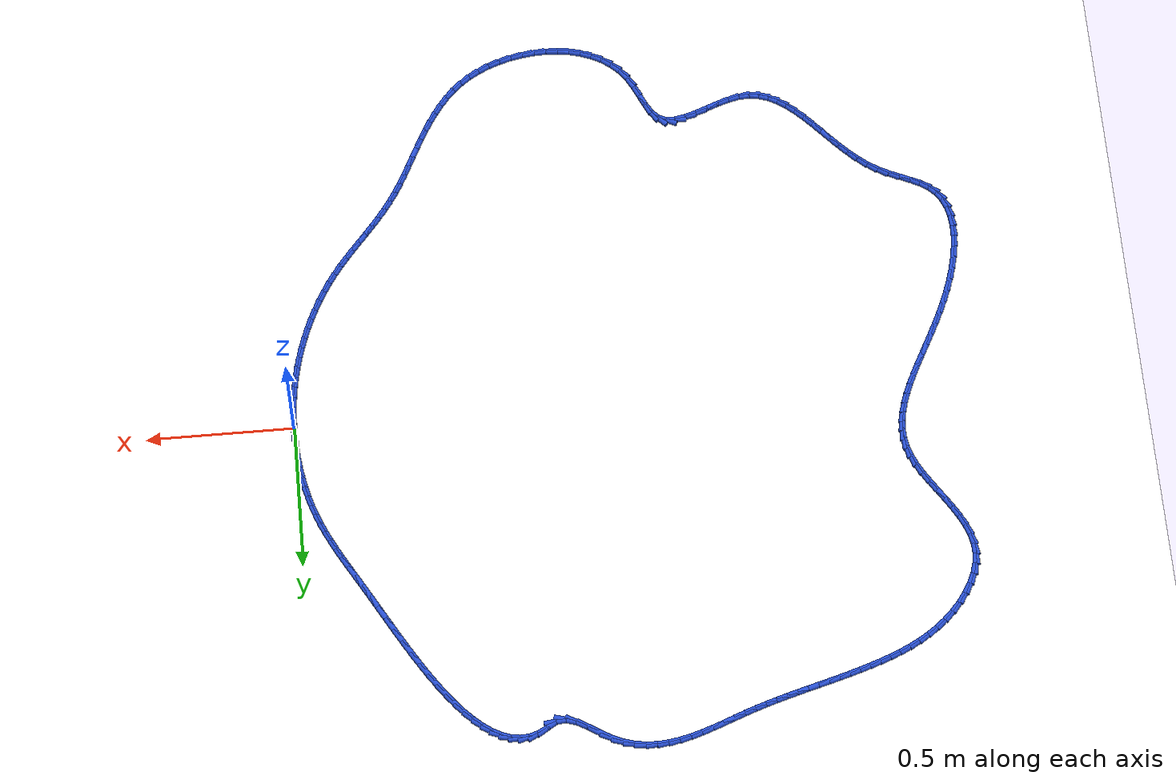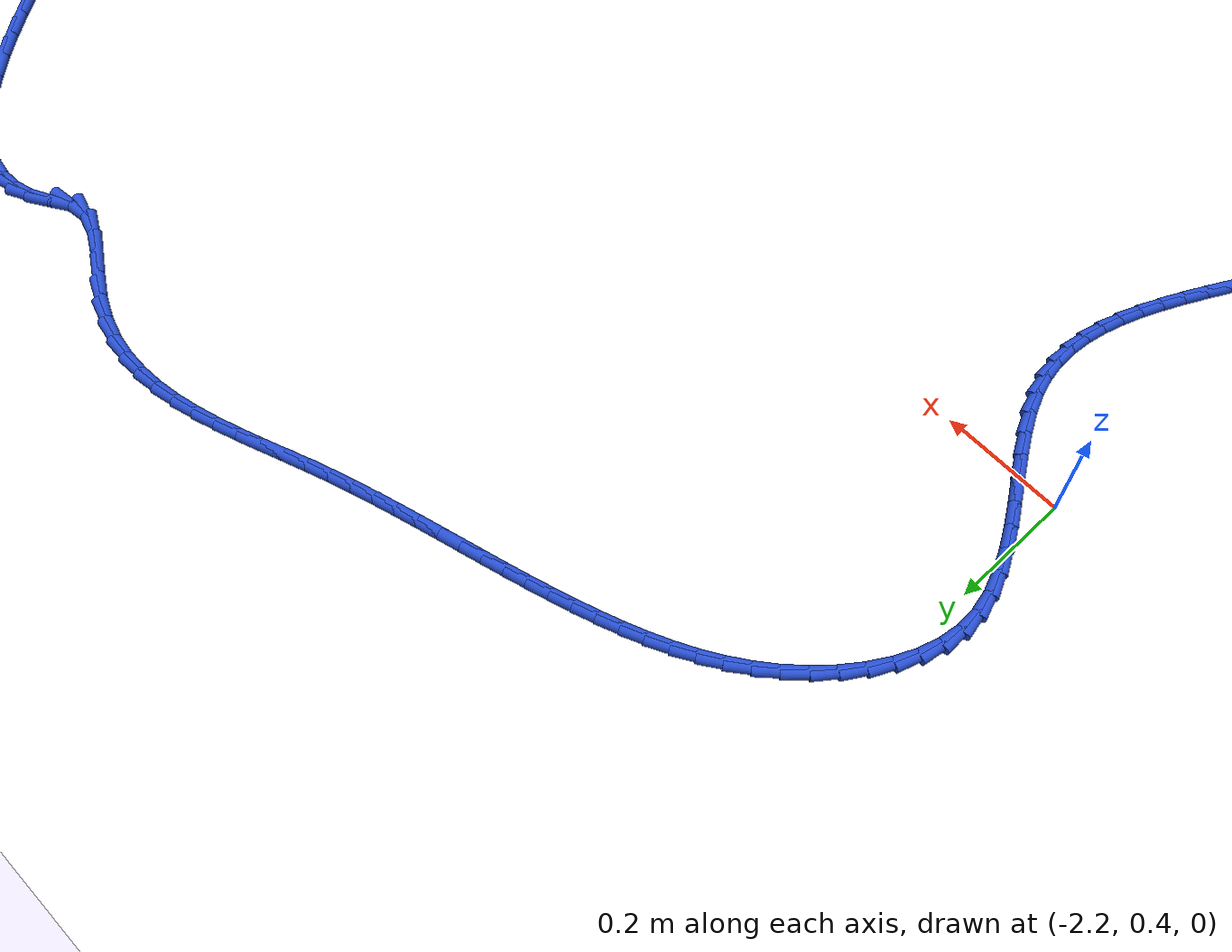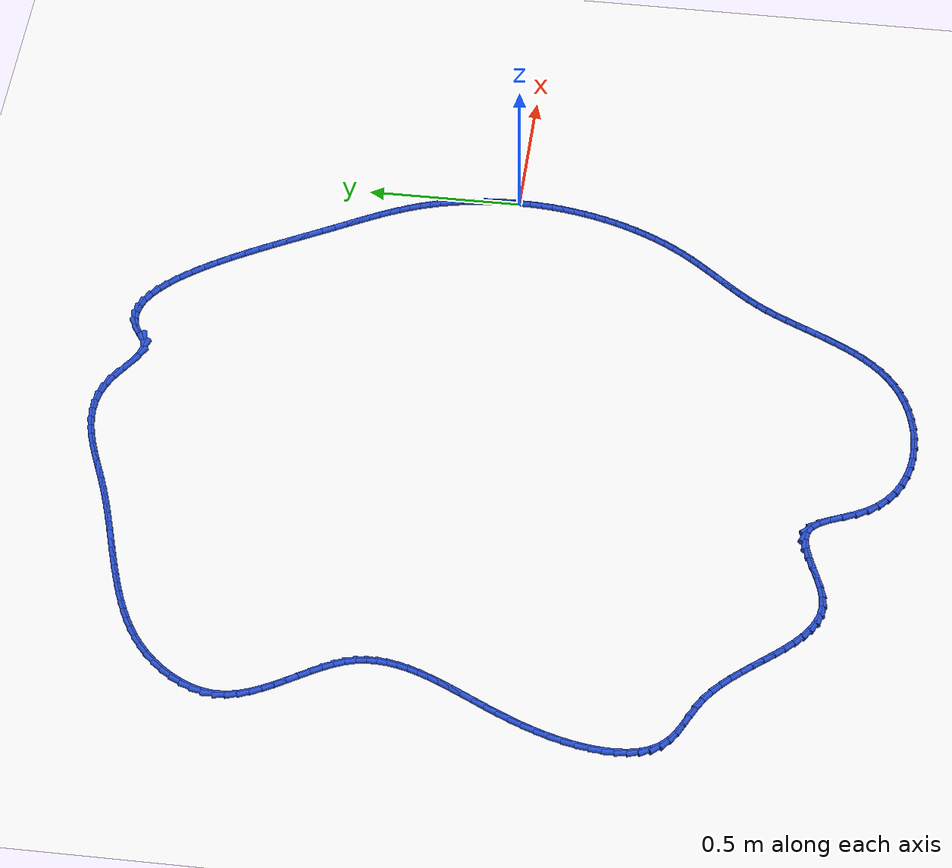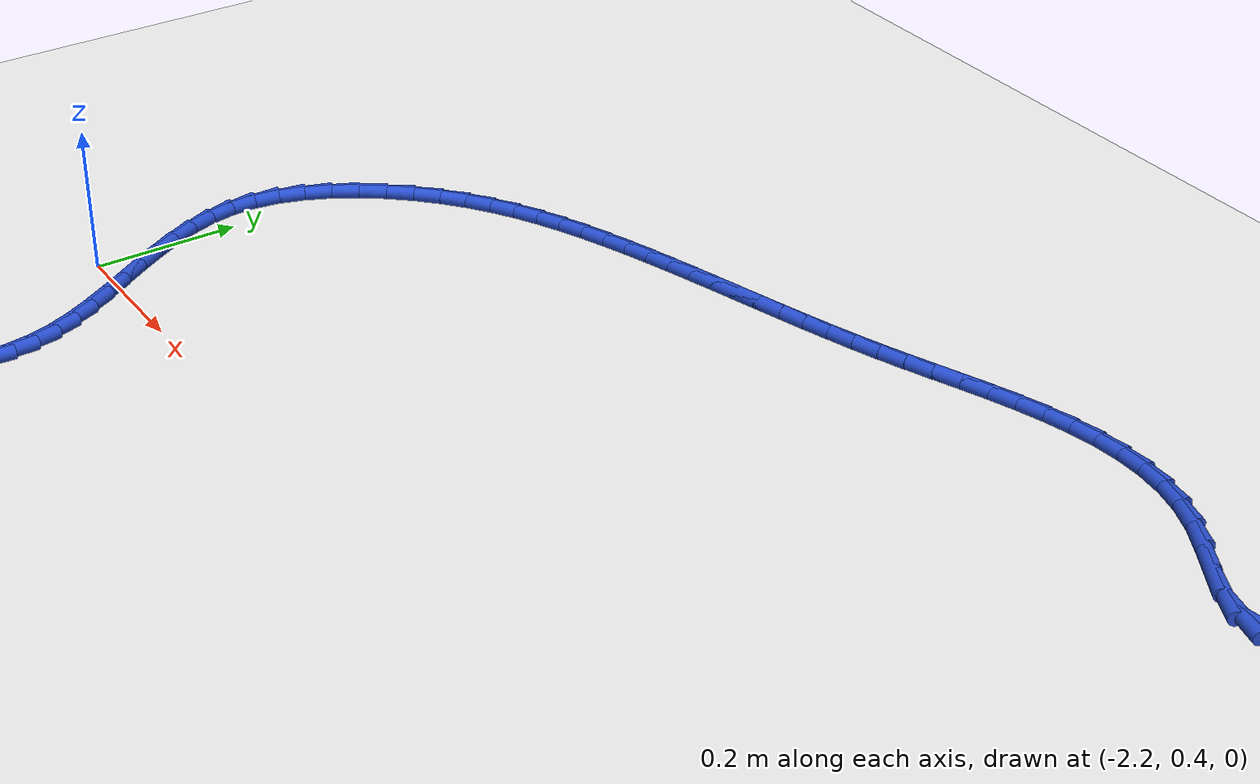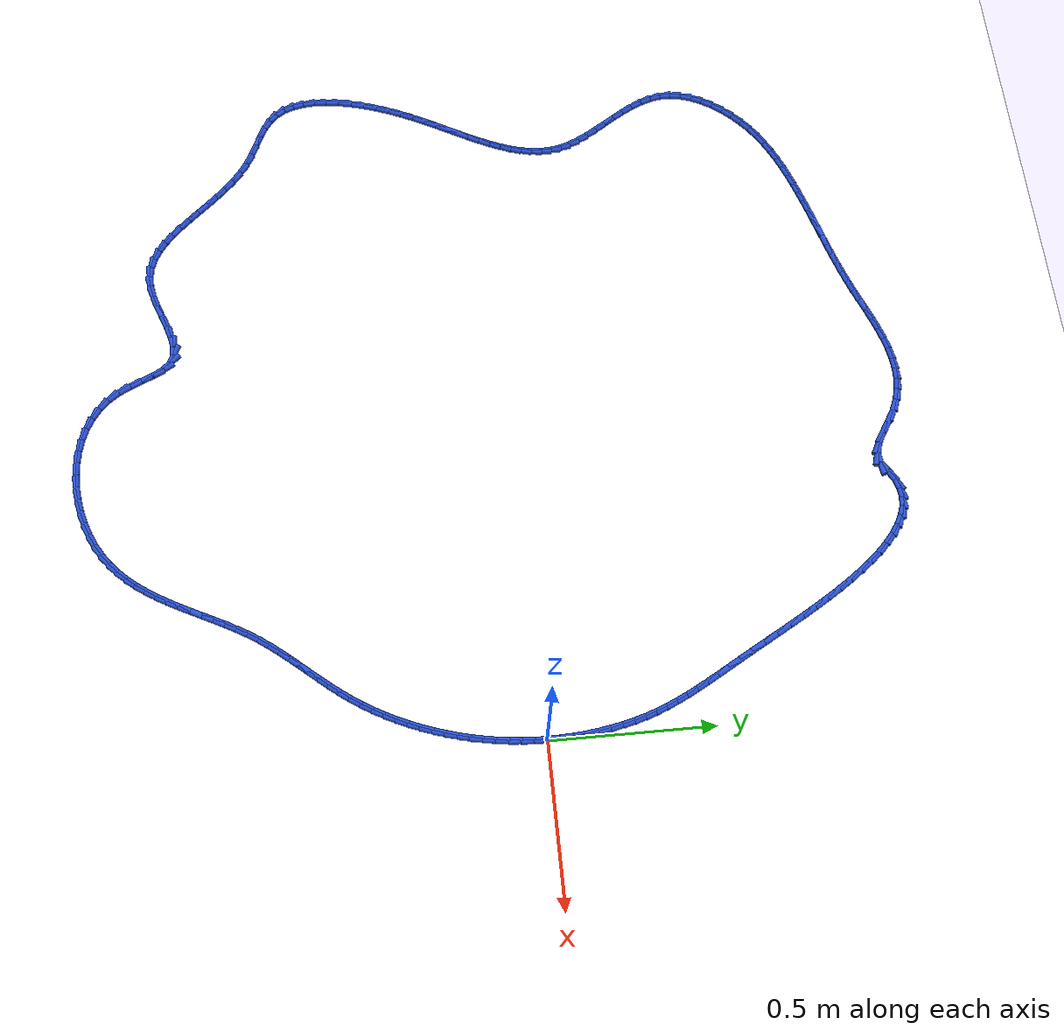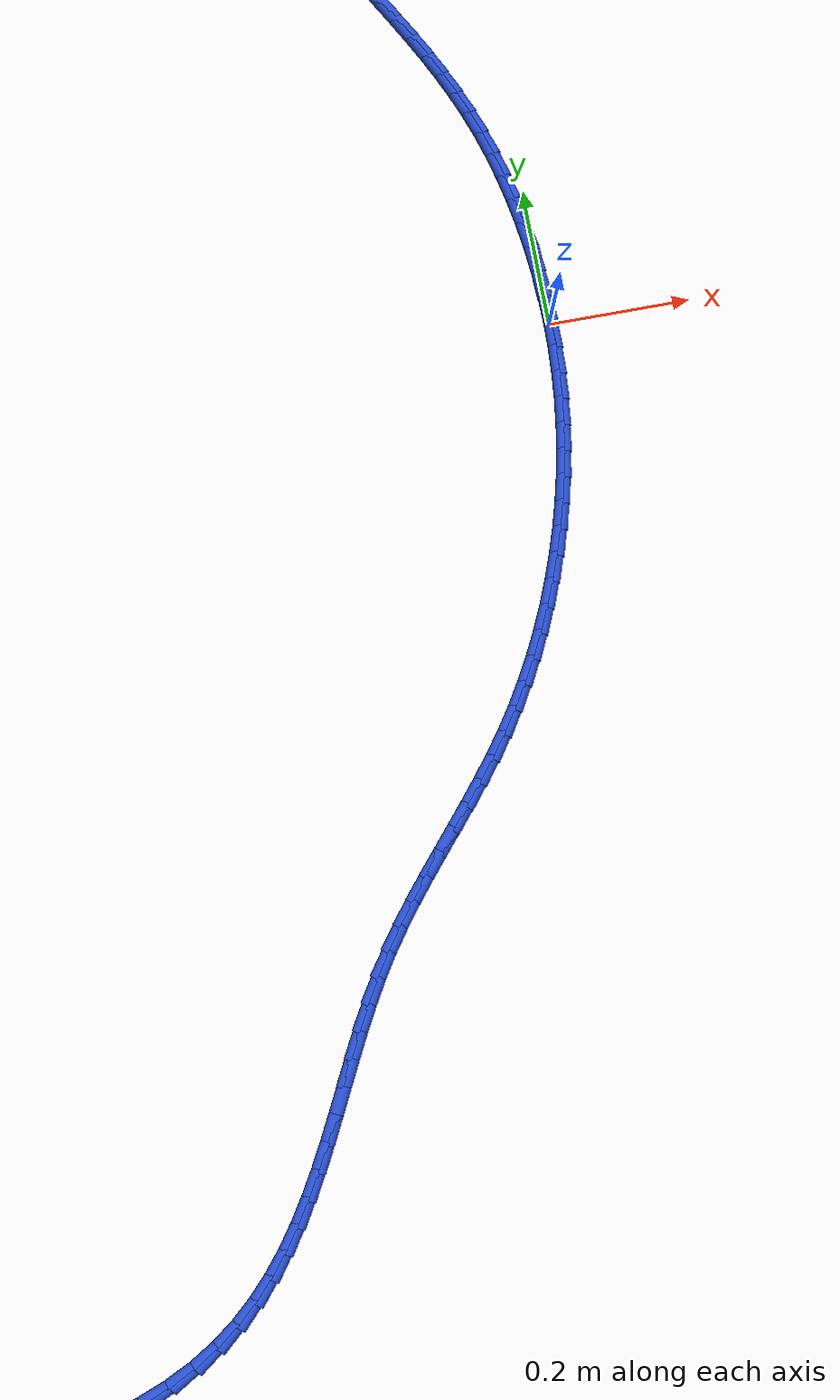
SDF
<sdf version="1.6">
 <world name="default">
  <light name="sun" type="directional">
   <pose>0 0 10 0 -0 0</pose>
   <diffuse>0.8 0.8 0.8 1</diffuse>
   <specular>0.2 0.2 0.2 1</specular>
   <attenuation>
    <range>1000</range>
    <constant>0.9</constant>
    <linear>0.01</linear>
    <quadratic>0.001</quadratic>
   </attenuation>
   <direction>-0.5 0.1 -0.9</direction>
  </light>
  <model name="ground_plane">
   <static>1</static>
   <link name="link">
    <collision name="collision">
     <geometry><plane><normal>0 0 1</normal><size>100 100</size></plane></geometry>
     <surface><friction><ode><mu>100</mu><mu2>50</mu2></ode></friction></surface>
    </collision>
    <visual name="visual">
     <cast_shadows>0</cast_shadows>
     <geometry><plane><normal>0 0 1</normal><size>100 100</size></plane></geometry>
     <material>
      <script><uri>file://media/materials/scripts/gazebo.material</uri><name>Gazebo/WhiteGlow</name></script>
     </material>
    </visual>
   </link>
  </model>
  <gravity>0 0 -9.8</gravity>
  <magnetic_field>6e-06 2.3e-05 -4.2e-05</magnetic_field>
  <atmosphere type="adiabatic"/>
  <physics name="default_physics" default="0" type="ode">
   <max_step_size>0.001</max_step_size>
   <real_time_factor>1</real_time_factor>
   <real_time_update_rate>1000</real_time_update_rate>
  </physics>
  <scene><ambient>0.4 0.4 0.4 1</ambient><background>0.7 0.7 0.7 1</background><shadows>1</shadows></scene>
  <spherical_coordinates>
   <surface_model>EARTH_WGS84</surface_model>
   <latitude_deg>0</latitude_deg>
   <longitude_deg>0</longitude_deg>
   <elevation>0</elevation>
   <heading_deg>0</heading_deg>
  </spherical_coordinates>
  <model name="line">
   <link name="link_0">
    <pose>1.6479873021779667e-17 -9.020562075079397e-17 0.01 0 1.57 -1.5525866050598032</pose>
    <collision name="collision">
     <geometry><cylinder><radius>0.01</radius><length>0.08</length></cylinder></geometry>
    </collision>
    <visual name="visual">
     <material>
      <script><name>Gazebo/Blue</name><uri>file://media/materials/scripts/gazebo.material</uri></script>
     </material>
     <geometry><cylinder><radius>0.01</radius><length>0.08</length></cylinder></geometry>
    </visual>
   </link>
   <link name="link_1">
    <pose>-0.0006907679868224856 0.037929829114566306 0.01 0 1.57 -1.5156297816635451</pose>
    <collision name="collision">
     <geometry><cylinder><radius>0.01</radius><length>0.08</length></cylinder></geometry>
    </collision>
    <visual name="visual">
     <material>
      <script><name>Gazebo/Blue</name><uri>file://media/materials/scripts/gazebo.material</uri></script>
     </material>
     <geometry><cylinder><radius>0.01</radius><length>0.08</length></cylinder></geometry>
    </visual>
   </link>
   <link name="link_2">
    <pose>-0.002787971782735226 0.07590711865418806 0.01 0 1.57 -1.47872899902266</pose>
    <collision name="collision">
     <geometry><cylinder><radius>0.01</radius><length>0.08</length></cylinder></geometry>
    </collision>
    <visual name="visual">
     <material>
      <script><name>Gazebo/Blue</name><uri>file://media/materials/scripts/gazebo.material</uri></script>
     </material>
     <geometry><cylinder><radius>0.01</radius><length>0.08</length></cylinder></geometry>
    </visual>
   </link>
   <link name="link_3">
    <pose>-0.006281897958674518 0.11374951848862565 0.01 0 1.57 -1.4414515022735026</pose>
    <collision name="collision">
     <geometry><cylinder><radius>0.01</radius><length>0.08</length></cylinder></geometry>
    </collision>
    <visual name="visual">
     <material>
      <script><name>Gazebo/Blue</name><uri>file://media/materials/scripts/gazebo.material</uri></script>
     </material>
     <geometry><cylinder><radius>0.01</radius><length>0.08</length></cylinder></geometry>
    </visual>
   </link>
   <link name="link_4">
    <pose>-0.011162833085576675 0.15127467848763962 0.01 0 1.57 -1.4033543646934457</pose>
    <collision name="collision">
     <geometry><cylinder><radius>0.01</radius><length>0.08</length></cylinder></geometry>
    </collision>
    <visual name="visual">
     <material>
      <script><name>Gazebo/Blue</name><uri>file://media/materials/scripts/gazebo.material</uri></script>
     </material>
     <geometry><cylinder><radius>0.01</radius><length>0.08</length></cylinder></geometry>
    </visual>
   </link>
   <link name="link_5">
    <pose>-0.017421063734378003 0.18830024852099056 0.01 0 1.57 -1.3639714678418755</pose>
    <collision name="collision">
     <geometry><cylinder><radius>0.01</radius><length>0.08</length></cylinder></geometry>
    </collision>
    <visual name="visual">
     <material>
      <script><name>Gazebo/Blue</name><uri>file://media/materials/scripts/gazebo.material</uri></script>
     </material>
     <geometry><cylinder><radius>0.01</radius><length>0.08</length></cylinder></geometry>
    </visual>
   </link>
   <link name="link_6">
    <pose>-0.025046876476014824 0.22464387845843903 0.01 0 1.57 -1.3227998943592105</pose>
    <collision name="collision">
     <geometry><cylinder><radius>0.01</radius><length>0.08</length></cylinder></geometry>
    </collision>
    <visual name="visual">
     <material>
      <script><name>Gazebo/Blue</name><uri>file://media/materials/scripts/gazebo.material</uri></script>
     </material>
     <geometry><cylinder><radius>0.01</radius><length>0.08</length></cylinder></geometry>
    </visual>
   </link>
   <link name="link_7">
    <pose>-0.03403055788142345 0.2601232181697456 0.01 0 1.57 -1.2792855298626473</pose>
    <collision name="collision">
     <geometry><cylinder><radius>0.01</radius><length>0.08</length></cylinder></geometry>
    </collision>
    <visual name="visual">
     <material>
      <script><name>Gazebo/Blue</name><uri>file://media/materials/scripts/gazebo.material</uri></script>
     </material>
     <geometry><cylinder><radius>0.01</radius><length>0.08</length></cylinder></geometry>
    </visual>
   </link>
   <link name="link_8">
    <pose>-0.04436239452154017 0.2945559175246707 0.01 0 1.57 -1.2337829482422613</pose>
    <collision name="collision">
     <geometry><cylinder><radius>0.01</radius><length>0.08</length></cylinder></geometry>
    </collision>
    <visual name="visual">
     <material>
      <script><name>Gazebo/Blue</name><uri>file://media/materials/scripts/gazebo.material</uri></script>
     </material>
     <geometry><cylinder><radius>0.01</radius><length>0.08</length></cylinder></geometry>
    </visual>
   </link>
   <link name="link_9">
    <pose>-0.056025664388597664 0.327843397632249 0.01 0 1.57 -1.190408357682</pose>
    <collision name="collision">
     <geometry><cylinder><radius>0.01</radius><length>0.08</length></cylinder></geometry>
    </collision>
    <visual name="visual">
     <material>
      <script><name>Gazebo/Blue</name><uri>file://media/materials/scripts/gazebo.material</uri></script>
     </material>
     <geometry><cylinder><radius>0.01</radius><length>0.08</length></cylinder></geometry>
    </visual>
   </link>
   <link name="link_10">
    <pose>-0.06897511160874324 0.3602281355308742 0.01 0 1.57 -1.1513973339295231</pose>
    <collision name="collision">
     <geometry><cylinder><radius>0.01</radius><length>0.08</length></cylinder></geometry>
    </collision>
    <visual name="visual">
     <material>
      <script><name>Gazebo/Blue</name><uri>file://media/materials/scripts/gazebo.material</uri></script>
     </material>
     <geometry><cylinder><radius>0.01</radius><length>0.08</length></cylinder></geometry>
    </visual>
   </link>
   <link name="link_11">
    <pose>-0.08315821973641305 0.3920393914878643 0.01 0 1.57 -1.1178304396316956</pose>
    <collision name="collision">
     <geometry><cylinder><radius>0.01</radius><length>0.08</length></cylinder></geometry>
    </collision>
    <visual name="visual">
     <material>
      <script><name>Gazebo/Blue</name><uri>file://media/materials/scripts/gazebo.material</uri></script>
     </material>
     <geometry><cylinder><radius>0.01</radius><length>0.08</length></cylinder></geometry>
    </visual>
   </link>
   <link name="link_12">
    <pose>-0.09852247232458754 0.4236064257879374 0.01 0 1.57 -1.090436765348096</pose>
    <collision name="collision">
     <geometry><cylinder><radius>0.01</radius><length>0.08</length></cylinder></geometry>
    </collision>
    <visual name="visual">
     <material>
      <script><name>Gazebo/Blue</name><uri>file://media/materials/scripts/gazebo.material</uri></script>
     </material>
     <geometry><cylinder><radius>0.01</radius><length>0.08</length></cylinder></geometry>
    </visual>
   </link>
   <link name="link_13">
    <pose>-0.11501535292624723 0.4552584987158111 0.01 0 1.57 -1.0695709780602856</pose>
    <collision name="collision">
     <geometry><cylinder><radius>0.01</radius><length>0.08</length></cylinder></geometry>
    </collision>
    <visual name="visual">
     <material>
      <script><name>Gazebo/Blue</name><uri>file://media/materials/scripts/gazebo.material</uri></script>
     </material>
     <geometry><cylinder><radius>0.01</radius><length>0.08</length></cylinder></geometry>
    </visual>
   </link>
   <link name="link_14">
    <pose>-0.13258434509437264 0.48732487055620377 0.01 0 1.57 -1.0552405589719425</pose>
    <collision name="collision">
     <geometry><cylinder><radius>0.01</radius><length>0.08</length></cylinder></geometry>
    </collision>
    <visual name="visual">
     <material>
      <script><name>Gazebo/Blue</name><uri>file://media/materials/scripts/gazebo.material</uri></script>
     </material>
     <geometry><cylinder><radius>0.01</radius><length>0.08</length></cylinder></geometry>
    </visual>
   </link>
   <link name="link_15">
    <pose>-0.15117693238194407 0.5201348015938329 0.01 0 1.57 -1.0471654375168649</pose>
    <collision name="collision">
     <geometry><cylinder><radius>0.01</radius><length>0.08</length></cylinder></geometry>
    </collision>
    <visual name="visual">
     <material>
      <script><name>Gazebo/Blue</name><uri>file://media/materials/scripts/gazebo.material</uri></script>
     </material>
     <geometry><cylinder><radius>0.01</radius><length>0.08</length></cylinder></geometry>
    </visual>
   </link>
   <link name="link_16">
    <pose>-0.17074059834194216 0.5540175521134164 0.01 0 1.57 -1.044851528452268</pose>
    <collision name="collision">
     <geometry><cylinder><radius>0.01</radius><length>0.08</length></cylinder></geometry>
    </collision>
    <visual name="visual">
     <material>
      <script><name>Gazebo/Blue</name><uri>file://media/materials/scripts/gazebo.material</uri></script>
     </material>
     <geometry><cylinder><radius>0.01</radius><length>0.08</length></cylinder></geometry>
    </visual>
   </link>
   <link name="link_17">
    <pose>-0.19122282652734737 0.5893023823996727 0.01 0 1.57 -1.0476641340067645</pose>
    <collision name="collision">
     <geometry><cylinder><radius>0.01</radius><length>0.08</length></cylinder></geometry>
    </collision>
    <visual name="visual">
     <material>
      <script><name>Gazebo/Blue</name><uri>file://media/materials/scripts/gazebo.material</uri></script>
     </material>
     <geometry><cylinder><radius>0.01</radius><length>0.08</length></cylinder></geometry>
    </visual>
   </link>
   <link name="link_18">
    <pose>-0.21257110049114006 0.6263185527373194 0.01 0 1.57 -1.0535643067097797</pose>
    <collision name="collision">
     <geometry><cylinder><radius>0.01</radius><length>0.08</length></cylinder></geometry>
    </collision>
    <visual name="visual">
     <material>
      <script><name>Gazebo/Blue</name><uri>file://media/materials/scripts/gazebo.material</uri></script>
     </material>
     <geometry><cylinder><radius>0.01</radius><length>0.08</length></cylinder></geometry>
    </visual>
   </link>
   <link name="link_19">
    <pose>-0.23473496080791495 0.6652782340910546 0.01 0 1.57 -1.0561494278433792</pose>
    <collision name="collision">
     <geometry><cylinder><radius>0.01</radius><length>0.08</length></cylinder></geometry>
    </collision>
    <visual name="visual">
     <material>
      <script><name>Gazebo/Blue</name><uri>file://media/materials/scripts/gazebo.material</uri></script>
     </material>
     <geometry><cylinder><radius>0.01</radius><length>0.08</length></cylinder></geometry>
    </visual>
   </link>
   <link name="link_20">
    <pose>-0.2576736125166838 0.7058434789634105 0.01 0 1.57 -1.054127906995681</pose>
    <collision name="collision">
     <geometry><cylinder><radius>0.01</radius><length>0.08</length></cylinder></geometry>
    </collision>
    <visual name="visual">
     <material>
      <script><name>Gazebo/Blue</name><uri>file://media/materials/scripts/gazebo.material</uri></script>
     </material>
     <geometry><cylinder><radius>0.01</radius><length>0.08</length></cylinder></geometry>
    </visual>
   </link>
   <link name="link_21">
    <pose>-0.28134909642565403 0.7475149228428535 0.01 0 1.57 -1.0478187644866925</pose>
    <collision name="collision">
     <geometry><cylinder><radius>0.01</radius><length>0.08</length></cylinder></geometry>
    </collision>
    <visual name="visual">
     <material>
      <script><name>Gazebo/Blue</name><uri>file://media/materials/scripts/gazebo.material</uri></script>
     </material>
     <geometry><cylinder><radius>0.01</radius><length>0.08</length></cylinder></geometry>
    </visual>
   </link>
   <link name="link_22">
    <pose>-0.3057234537155131 0.7897931800156041 0.01 0 1.57 -1.0372772700623707</pose>
    <collision name="collision">
     <geometry><cylinder><radius>0.01</radius><length>0.08</length></cylinder></geometry>
    </collision>
    <visual name="visual">
     <material>
      <script><name>Gazebo/Blue</name><uri>file://media/materials/scripts/gazebo.material</uri></script>
     </material>
     <geometry><cylinder><radius>0.01</radius><length>0.08</length></cylinder></geometry>
    </visual>
   </link>
   <link name="link_23">
    <pose>-0.33075872556694874 0.8321788647678828 0.01 0 1.57 -1.0223267759087806</pose>
    <collision name="collision">
     <geometry><cylinder><radius>0.01</radius><length>0.08</length></cylinder></geometry>
    </collision>
    <visual name="visual">
     <material>
      <script><name>Gazebo/Blue</name><uri>file://media/materials/scripts/gazebo.material</uri></script>
     </material>
     <geometry><cylinder><radius>0.01</radius><length>0.08</length></cylinder></geometry>
    </visual>
   </link>
   <link name="link_24">
    <pose>-0.35641695316064875 0.8741725913859111 0.01 0 1.57 -1.002559172554032</pose>
    <collision name="collision">
     <geometry><cylinder><radius>0.01</radius><length>0.08</length></cylinder></geometry>
    </collision>
    <visual name="visual">
     <material>
      <script><name>Gazebo/Blue</name><uri>file://media/materials/scripts/gazebo.material</uri></script>
     </material>
     <geometry><cylinder><radius>0.01</radius><length>0.08</length></cylinder></geometry>
    </visual>
   </link>
   <link name="link_25">
    <pose>-0.38266017767730065 0.9152749741559092 0.01 0 1.57 -0.9773079850060323</pose>
    <collision name="collision">
     <geometry><cylinder><radius>0.01</radius><length>0.08</length></cylinder></geometry>
    </collision>
    <visual name="visual">
     <material>
      <script><name>Gazebo/Blue</name><uri>file://media/materials/scripts/gazebo.material</uri></script>
     </material>
     <geometry><cylinder><radius>0.01</radius><length>0.08</length></cylinder></geometry>
    </visual>
   </link>
   <link name="link_26">
    <pose>-0.40945044029759214 0.9549866273640981 0.01 0 1.57 -0.9455930715460027</pose>
    <collision name="collision">
     <geometry><cylinder><radius>0.01</radius><length>0.08</length></cylinder></geometry>
    </collision>
    <visual name="visual">
     <material>
      <script><name>Gazebo/Blue</name><uri>file://media/materials/scripts/gazebo.material</uri></script>
     </material>
     <geometry><cylinder><radius>0.01</radius><length>0.08</length></cylinder></geometry>
    </visual>
   </link>
   <link name="link_27">
    <pose>-0.43674978220221095 0.9928081652966988 0.01 0 1.57 -0.9060322101747197</pose>
    <collision name="collision">
     <geometry><cylinder><radius>0.01</radius><length>0.08</length></cylinder></geometry>
    </collision>
    <visual name="visual">
     <material>
      <script><name>Gazebo/Blue</name><uri>file://media/materials/scripts/gazebo.material</uri></script>
     </material>
     <geometry><cylinder><radius>0.01</radius><length>0.08</length></cylinder></geometry>
    </visual>
   </link>
   <link name="link_28">
    <pose>-0.46452024457184465 1.0282402022399317 0.01 0 1.57 -0.8567133410214515</pose>
    <collision name="collision">
     <geometry><cylinder><radius>0.01</radius><length>0.08</length></cylinder></geometry>
    </collision>
    <visual name="visual">
     <material>
      <script><name>Gazebo/Blue</name><uri>file://media/materials/scripts/gazebo.material</uri></script>
     </material>
     <geometry><cylinder><radius>0.01</radius><length>0.08</length></cylinder></geometry>
    </visual>
   </link>
   <link name="link_29">
    <pose>-0.4927238685871807 1.0607833524800176 0.01 0 1.57 -0.795025836705056</pose>
    <collision name="collision">
     <geometry><cylinder><radius>0.01</radius><length>0.08</length></cylinder></geometry>
    </collision>
    <visual name="visual">
     <material>
      <script><name>Gazebo/Blue</name><uri>file://media/materials/scripts/gazebo.material</uri></script>
     </material>
     <geometry><cylinder><radius>0.01</radius><length>0.08</length></cylinder></geometry>
    </visual>
   </link>
   <link name="link_30">
    <pose>-0.5213226954289072 1.0899382303031777 0.01 0 1.57 -0.7174720752192506</pose>
    <collision name="collision">
     <geometry><cylinder><radius>0.01</radius><length>0.08</length></cylinder></geometry>
    </collision>
    <visual name="visual">
     <material>
      <script><name>Gazebo/Blue</name><uri>file://media/materials/scripts/gazebo.material</uri></script>
     </material>
     <geometry><cylinder><radius>0.01</radius><length>0.08</length></cylinder></geometry>
    </visual>
   </link>
   <link name="link_31">
    <pose>-0.5502787662777112 1.1152054499956319 0.01 0 1.57 -0.6195526562315516</pose>
    <collision name="collision">
     <geometry><cylinder><radius>0.01</radius><length>0.08</length></cylinder></geometry>
    </collision>
    <visual name="visual">
     <material>
      <script><name>Gazebo/Blue</name><uri>file://media/materials/scripts/gazebo.material</uri></script>
     </material>
     <geometry><cylinder><radius>0.01</radius><length>0.08</length></cylinder></geometry>
    </visual>
   </link>
   <link name="link_32">
    <pose>-0.5795541223142812 1.136085625843602 0.01 0 1.57 -0.4960008967441921</pose>
    <collision name="collision">
     <geometry><cylinder><radius>0.01</radius><length>0.08</length></cylinder></geometry>
    </collision>
    <visual name="visual">
     <material>
      <script><name>Gazebo/Blue</name><uri>file://media/materials/scripts/gazebo.material</uri></script>
     </material>
     <geometry><cylinder><radius>0.01</radius><length>0.08</length></cylinder></geometry>
    </visual>
   </link>
   <link name="link_33">
    <pose>-0.6091108047193043 1.1520793721333085 0.01 0 1.57 -0.3419835887315888</pose>
    <collision name="collision">
     <geometry><cylinder><radius>0.01</radius><length>0.08</length></cylinder></geometry>
    </collision>
    <visual name="visual">
     <material>
      <script><name>Gazebo/Blue</name><uri>file://media/materials/scripts/gazebo.material</uri></script>
     </material>
     <geometry><cylinder><radius>0.01</radius><length>0.08</length></cylinder></geometry>
    </visual>
   </link>
   <link name="link_34">
    <pose>-0.638910854673468 1.1626873031509715 0.01 0 1.57 -0.15611493687410552</pose>
    <collision name="collision">
     <geometry><cylinder><radius>0.01</radius><length>0.08</length></cylinder></geometry>
    </collision>
    <visual name="visual">
     <material>
      <script><name>Gazebo/Blue</name><uri>file://media/materials/scripts/gazebo.material</uri></script>
     </material>
     <geometry><cylinder><radius>0.01</radius><length>0.08</length></cylinder></geometry>
    </visual>
   </link>
   <link name="link_35">
    <pose>-0.6689163133574603 1.1674100331828123 0.01 0 1.57 0.05502218211995027</pose>
    <collision name="collision">
     <geometry><cylinder><radius>0.01</radius><length>0.08</length></cylinder></geometry>
    </collision>
    <visual name="visual">
     <material>
      <script><name>Gazebo/Blue</name><uri>file://media/materials/scripts/gazebo.material</uri></script>
     </material>
     <geometry><cylinder><radius>0.01</radius><length>0.08</length></cylinder></geometry>
    </visual>
   </link>
   <link name="link_36">
    <pose>-0.6990892219519687 1.165748176515052 0.01 0 1.57 0.2748792234774522</pose>
    <collision name="collision">
     <geometry><cylinder><radius>0.01</radius><length>0.08</length></cylinder></geometry>
    </collision>
    <visual name="visual">
     <material>
      <script><name>Gazebo/Blue</name><uri>file://media/materials/scripts/gazebo.material</uri></script>
     </material>
     <geometry><cylinder><radius>0.01</radius><length>0.08</length></cylinder></geometry>
    </visual>
   </link>
   <link name="link_37">
    <pose>-0.729391621637681 1.1572023474339108 0.01 0 1.57 0.48273416932443225</pose>
    <collision name="collision">
     <geometry><cylinder><radius>0.01</radius><length>0.08</length></cylinder></geometry>
    </collision>
    <visual name="visual">
     <material>
      <script><name>Gazebo/Blue</name><uri>file://media/materials/scripts/gazebo.material</uri></script>
     </material>
     <geometry><cylinder><radius>0.01</radius><length>0.08</length></cylinder></geometry>
    </visual>
   </link>
   <link name="link_38">
    <pose>-0.7597855535952849 1.1412731602256097 0.01 0 1.57 0.5669502036484709</pose>
    <collision name="collision">
     <geometry><cylinder><radius>0.01</radius><length>0.08</length></cylinder></geometry>
    </collision>
    <visual name="visual">
     <material>
      <script><name>Gazebo/Blue</name><uri>file://media/materials/scripts/gazebo.material</uri></script>
     </material>
     <geometry><cylinder><radius>0.01</radius><length>0.08</length></cylinder></geometry>
    </visual>
   </link>
   <link name="link_39">
    <pose>-0.7905588839530812 1.121680576080125 0.01 0 1.57 0.12630331599617128</pose>
    <collision name="collision">
     <geometry><cylinder><radius>0.01</radius><length>0.08</length></cylinder></geometry>
    </collision>
    <visual name="visual">
     <material>
      <script><name>Gazebo/Blue</name><uri>file://media/materials/scripts/gazebo.material</uri></script>
     </material>
     <geometry><cylinder><radius>0.01</radius><length>0.08</length></cylinder></geometry>
    </visual>
   </link>
   <link name="link_40">
    <pose>-0.8231798651433603 1.1175383884031536 0.01 0 1.57 -0.28693302493927386</pose>
    <collision name="collision">
     <geometry><cylinder><radius>0.01</radius><length>0.08</length></cylinder></geometry>
    </collision>
    <visual name="visual">
     <material>
      <script><name>Gazebo/Blue</name><uri>file://media/materials/scripts/gazebo.material</uri></script>
     </material>
     <geometry><cylinder><radius>0.01</radius><length>0.08</length></cylinder></geometry>
    </visual>
   </link>
   <link name="link_41">
    <pose>-0.8575336866154382 1.127675367712229 0.01 0 1.57 -0.4951000127802804</pose>
    <collision name="collision">
     <geometry><cylinder><radius>0.01</radius><length>0.08</length></cylinder></geometry>
    </collision>
    <visual name="visual">
     <material>
      <script><name>Gazebo/Blue</name><uri>file://media/materials/scripts/gazebo.material</uri></script>
     </material>
     <geometry><cylinder><radius>0.01</radius><length>0.08</length></cylinder></geometry>
    </visual>
   </link>
   <link name="link_42">
    <pose>-0.893195635019809 1.1469312883190548 0.01 0 1.57 -0.5659204765657412</pose>
    <collision name="collision">
     <geometry><cylinder><radius>0.01</radius><length>0.08</length></cylinder></geometry>
    </collision>
    <visual name="visual">
     <material>
      <script><name>Gazebo/Blue</name><uri>file://media/materials/scripts/gazebo.material</uri></script>
     </material>
     <geometry><cylinder><radius>0.01</radius><length>0.08</length></cylinder></geometry>
    </visual>
   </link>
   <link name="link_43">
    <pose>-0.9297409970069682 1.1701459245353345 0.01 0 1.57 -0.5366493144910013</pose>
    <collision name="collision">
     <geometry><cylinder><radius>0.01</radius><length>0.08</length></cylinder></geometry>
    </collision>
    <visual name="visual">
     <material>
      <script><name>Gazebo/Blue</name><uri>file://media/materials/scripts/gazebo.material</uri></script>
     </material>
     <geometry><cylinder><radius>0.01</radius><length>0.08</length></cylinder></geometry>
    </visual>
   </link>
   <link name="link_44">
    <pose>-0.9667450593738129 1.1921590527190467 0.01 0 1.57 -0.4216733075283665</pose>
    <collision name="collision">
     <geometry><cylinder><radius>0.01</radius><length>0.08</length></cylinder></geometry>
    </collision>
    <visual name="visual">
     <material>
      <script><name>Gazebo/Blue</name><uri>file://media/materials/scripts/gazebo.material</uri></script>
     </material>
     <geometry><cylinder><radius>0.01</radius><length>0.08</length></cylinder></geometry>
    </visual>
   </link>
   <link name="link_45">
    <pose>-1.0038543046584598 1.2088055572794447 0.01 0 1.57 -0.2866046705655975</pose>
    <collision name="collision">
     <geometry><cylinder><radius>0.01</radius><length>0.08</length></cylinder></geometry>
    </collision>
    <visual name="visual">
     <material>
      <script><name>Gazebo/Blue</name><uri>file://media/materials/scripts/gazebo.material</uri></script>
     </material>
     <geometry><cylinder><radius>0.01</radius><length>0.08</length></cylinder></geometry>
    </visual>
   </link>
   <link name="link_46">
    <pose>-1.0409892062057131 1.219749912051136 0.01 0 1.57 -0.15561622205311462</pose>
    <collision name="collision">
     <geometry><cylinder><radius>0.01</radius><length>0.08</length></cylinder></geometry>
    </collision>
    <visual name="visual">
     <material>
      <script><name>Gazebo/Blue</name><uri>file://media/materials/scripts/gazebo.material</uri></script>
     </material>
     <geometry><cylinder><radius>0.01</radius><length>0.08</length></cylinder></geometry>
    </visual>
   </link>
   <link name="link_47">
    <pose>-1.078136138515642 1.2255776961071945 0.01 0 1.57 -0.034897137562389546</pose>
    <collision name="collision">
     <geometry><cylinder><radius>0.01</radius><length>0.08</length></cylinder></geometry>
    </collision>
    <visual name="visual">
     <material>
      <script><name>Gazebo/Blue</name><uri>file://media/materials/scripts/gazebo.material</uri></script>
     </material>
     <geometry><cylinder><radius>0.01</radius><length>0.08</length></cylinder></geometry>
    </visual>
   </link>
   <link name="link_48">
    <pose>-1.1152814760883172 1.2268744885206933 0.01 0 1.57 0.0712128466700696</pose>
    <collision name="collision">
     <geometry><cylinder><radius>0.01</radius><length>0.08</length></cylinder></geometry>
    </collision>
    <visual name="visual">
     <material>
      <script><name>Gazebo/Blue</name><uri>file://media/materials/scripts/gazebo.material</uri></script>
     </material>
     <geometry><cylinder><radius>0.01</radius><length>0.08</length></cylinder></geometry>
    </visual>
   </link>
   <link name="link_49">
    <pose>-1.1524115934238095 1.2242258683647065 0.01 0 1.57 0.16055345264056176</pose>
    <collision name="collision">
     <geometry><cylinder><radius>0.01</radius><length>0.08</length></cylinder></geometry>
    </collision>
    <visual name="visual">
     <material>
      <script><name>Gazebo/Blue</name><uri>file://media/materials/scripts/gazebo.material</uri></script>
     </material>
     <geometry><cylinder><radius>0.01</radius><length>0.08</length></cylinder></geometry>
    </visual>
   </link>
   <link name="link_50">
    <pose>-1.1895128650221878 1.2182174147123064 0.01 0 1.57 0.23270062947565884</pose>
    <collision name="collision">
     <geometry><cylinder><radius>0.01</radius><length>0.08</length></cylinder></geometry>
    </collision>
    <visual name="visual">
     <material>
      <script><name>Gazebo/Blue</name><uri>file://media/materials/scripts/gazebo.material</uri></script>
     </material>
     <geometry><cylinder><radius>0.01</radius><length>0.08</length></cylinder></geometry>
    </visual>
   </link>
   <link name="link_51">
    <pose>-1.2265716653835232 1.2094347066365678 0.01 0 1.57 0.2882447322584531</pose>
    <collision name="collision">
     <geometry><cylinder><radius>0.01</radius><length>0.08</length></cylinder></geometry>
    </collision>
    <visual name="visual">
     <material>
      <script><name>Gazebo/Blue</name><uri>file://media/materials/scripts/gazebo.material</uri></script>
     </material>
     <geometry><cylinder><radius>0.01</radius><length>0.08</length></cylinder></geometry>
    </visual>
   </link>
   <link name="link_52">
    <pose>-1.2635743690078853 1.1984633232105633 0.01 0 1.57 0.32815750073493194</pose>
    <collision name="collision">
     <geometry><cylinder><radius>0.01</radius><length>0.08</length></cylinder></geometry>
    </collision>
    <visual name="visual">
     <material>
      <script><name>Gazebo/Blue</name><uri>file://media/materials/scripts/gazebo.material</uri></script>
     </material>
     <geometry><cylinder><radius>0.01</radius><length>0.08</length></cylinder></geometry>
    </visual>
   </link>
   <link name="link_53">
    <pose>-1.3005073503953455 1.1858888435073665 0.01 0 1.57 0.3533682459631565</pose>
    <collision name="collision">
     <geometry><cylinder><radius>0.01</radius><length>0.08</length></cylinder></geometry>
    </collision>
    <visual name="visual">
     <material>
      <script><name>Gazebo/Blue</name><uri>file://media/materials/scripts/gazebo.material</uri></script>
     </material>
     <geometry><cylinder><radius>0.01</radius><length>0.08</length></cylinder></geometry>
    </visual>
   </link>
   <link name="link_54">
    <pose>-1.3373569840459727 1.1722968466000514 0.01 0 1.57 0.3645234744854424</pose>
    <collision name="collision">
     <geometry><cylinder><radius>0.01</radius><length>0.08</length></cylinder></geometry>
    </collision>
    <visual name="visual">
     <material>
      <script><name>Gazebo/Blue</name><uri>file://media/materials/scripts/gazebo.material</uri></script>
     </material>
     <geometry><cylinder><radius>0.01</radius><length>0.08</length></cylinder></geometry>
    </visual>
   </link>
   <link name="link_55">
    <pose>-1.3741096444598373 1.1582729115616905 0.01 0 1.57 0.36186603263953043</pose>
    <collision name="collision">
     <geometry><cylinder><radius>0.01</radius><length>0.08</length></cylinder></geometry>
    </collision>
    <visual name="visual">
     <material>
      <script><name>Gazebo/Blue</name><uri>file://media/materials/scripts/gazebo.material</uri></script>
     </material>
     <geometry><cylinder><radius>0.01</radius><length>0.08</length></cylinder></geometry>
    </visual>
   </link>
   <link name="link_56">
    <pose>-1.4107517061370105 1.1444026174653583 0.01 0 1.57 0.3456758314015255</pose>
    <collision name="collision">
     <geometry><cylinder><radius>0.01</radius><length>0.08</length></cylinder></geometry>
    </collision>
    <visual name="visual">
     <material>
      <script><name>Gazebo/Blue</name><uri>file://media/materials/scripts/gazebo.material</uri></script>
     </material>
     <geometry><cylinder><radius>0.01</radius><length>0.08</length></cylinder></geometry>
    </visual>
   </link>
   <link name="link_57">
    <pose>-1.4472698155649242 1.1312511374072356 0.01 0 1.57 0.3245727060012548</pose>
    <collision name="collision">
     <geometry><cylinder><radius>0.01</radius><length>0.08</length></cylinder></geometry>
    </collision>
    <visual name="visual">
     <material>
      <script><name>Gazebo/Blue</name><uri>file://media/materials/scripts/gazebo.material</uri></script>
     </material>
     <geometry><cylinder><radius>0.01</radius><length>0.08</length></cylinder></geometry>
    </visual>
   </link>
   <link name="link_58">
    <pose>-1.4836556217022525 1.1190083317792414 0.01 0 1.57 0.3065445010094057</pose>
    <collision name="collision">
     <geometry><cylinder><radius>0.01</radius><length>0.08</length></cylinder></geometry>
    </collision>
    <visual name="visual">
     <material>
      <script><name>Gazebo/Blue</name><uri>file://media/materials/scripts/gazebo.material</uri></script>
     </material>
     <geometry><cylinder><radius>0.01</radius><length>0.08</length></cylinder></geometry>
    </visual>
   </link>
   <link name="link_59">
    <pose>-1.519905165270487 1.1075345669494088 0.01 0 1.57 0.29203368374038025</pose>
    <collision name="collision">
     <geometry><cylinder><radius>0.01</radius><length>0.08</length></cylinder></geometry>
    </collision>
    <visual name="visual">
     <material>
      <script><name>Gazebo/Blue</name><uri>file://media/materials/scripts/gazebo.material</uri></script>
     </material>
     <geometry><cylinder><radius>0.01</radius><length>0.08</length></cylinder></geometry>
    </visual>
   </link>
   <link name="link_60">
    <pose>-1.5560146361873424 1.0966790157705117 0.01 0 1.57 0.2811835927856022</pose>
    <collision name="collision">
     <geometry><cylinder><radius>0.01</radius><length>0.08</length></cylinder></geometry>
    </collision>
    <visual name="visual">
     <material>
      <script><name>Gazebo/Blue</name><uri>file://media/materials/scripts/gazebo.material</uri></script>
     </material>
     <geometry><cylinder><radius>0.01</radius><length>0.08</length></cylinder></geometry>
    </visual>
   </link>
   <link name="link_61">
    <pose>-1.5919802243705317 1.0862908510953242 0.01 0 1.57 0.27411110640501496</pose>
    <collision name="collision">
     <geometry><cylinder><radius>0.01</radius><length>0.08</length></cylinder></geometry>
    </collision>
    <visual name="visual">
     <material>
      <script><name>Gazebo/Blue</name><uri>file://media/materials/scripts/gazebo.material</uri></script>
     </material>
     <geometry><cylinder><radius>0.01</radius><length>0.08</length></cylinder></geometry>
    </visual>
   </link>
   <link name="link_62">
    <pose>-1.6277981197377693 1.0762192457766204 0.01 0 1.57 0.2709088959671338</pose>
    <collision name="collision">
     <geometry><cylinder><radius>0.01</radius><length>0.08</length></cylinder></geometry>
    </collision>
    <visual name="visual">
     <material>
      <script><name>Gazebo/Blue</name><uri>file://media/materials/scripts/gazebo.material</uri></script>
     </material>
     <geometry><cylinder><radius>0.01</radius><length>0.08</length></cylinder></geometry>
    </visual>
   </link>
   <link name="link_63">
    <pose>-1.663464512206771 1.0663133726671745 0.01 0 1.57 0.27164680582059736</pose>
    <collision name="collision">
     <geometry><cylinder><radius>0.01</radius><length>0.08</length></cylinder></geometry>
    </collision>
    <visual name="visual">
     <material>
      <script><name>Gazebo/Blue</name><uri>file://media/materials/scripts/gazebo.material</uri></script>
     </material>
     <geometry><cylinder><radius>0.01</radius><length>0.08</length></cylinder></geometry>
    </visual>
   </link>
   <link name="link_64">
    <pose>-1.6989755916952491 1.056422404619761 0.01 0 1.57 0.27637200443271176</pose>
    <collision name="collision">
     <geometry><cylinder><radius>0.01</radius><length>0.08</length></cylinder></geometry>
    </collision>
    <visual name="visual">
     <material>
      <script><name>Gazebo/Blue</name><uri>file://media/materials/scripts/gazebo.material</uri></script>
     </material>
     <geometry><cylinder><radius>0.01</radius><length>0.08</length></cylinder></geometry>
    </visual>
   </link>
   <link name="link_65">
    <pose>-1.7343275481209188 1.0463955144871533 0.01 0 1.57 0.2851076676518039</pose>
    <collision name="collision">
     <geometry><cylinder><radius>0.01</radius><length>0.08</length></cylinder></geometry>
    </collision>
    <visual name="visual">
     <material>
      <script><name>Gazebo/Blue</name><uri>file://media/materials/scripts/gazebo.material</uri></script>
     </material>
     <geometry><cylinder><radius>0.01</radius><length>0.08</length></cylinder></geometry>
    </visual>
   </link>
   <link name="link_66">
    <pose>-1.7695165714014949 1.036081875122126 0.01 0 1.57 0.29785008741014457</pose>
    <collision name="collision">
     <geometry><cylinder><radius>0.01</radius><length>0.08</length></cylinder></geometry>
    </collision>
    <visual name="visual">
     <material>
      <script><name>Gazebo/Blue</name><uri>file://media/materials/scripts/gazebo.material</uri></script>
     </material>
     <geometry><cylinder><radius>0.01</radius><length>0.08</length></cylinder></geometry>
    </visual>
   </link>
   <link name="link_67">
    <pose>-1.8045388514546898 1.0253306593774527 0.01 0 1.57 0.3145642561746845</pose>
    <collision name="collision">
     <geometry><cylinder><radius>0.01</radius><length>0.08</length></cylinder></geometry>
    </collision>
    <visual name="visual">
     <material>
      <script><name>Gazebo/Blue</name><uri>file://media/materials/scripts/gazebo.material</uri></script>
     </material>
     <geometry><cylinder><radius>0.01</radius><length>0.08</length></cylinder></geometry>
    </visual>
   </link>
   <link name="link_68">
    <pose>-1.8393905781982196 1.0139910401059082 0.01 0 1.57 0.3351785629790822</pose>
    <collision name="collision">
     <geometry><cylinder><radius>0.01</radius><length>0.08</length></cylinder></geometry>
    </collision>
    <visual name="visual">
     <material>
      <script><name>Gazebo/Blue</name><uri>file://media/materials/scripts/gazebo.material</uri></script>
     </material>
     <geometry><cylinder><radius>0.01</radius><length>0.08</length></cylinder></geometry>
    </visual>
   </link>
   <link name="link_69">
    <pose>-1.8740679286893163 1.0019121792608658 0.01 0 1.57 0.3606069490011486</pose>
    <collision name="collision">
     <geometry><cylinder><radius>0.01</radius><length>0.08</length></cylinder></geometry>
    </collision>
    <visual name="visual">
     <material>
      <script><name>Gazebo/Blue</name><uri>file://media/materials/scripts/gazebo.material</uri></script>
     </material>
     <geometry><cylinder><radius>0.01</radius><length>0.08</length></cylinder></geometry>
    </visual>
   </link>
   <link name="link_70">
    <pose>-1.9085339674809465 0.988915175583319 0.01 0 1.57 0.3940182166056302</pose>
    <collision name="collision">
     <geometry><cylinder><radius>0.01</radius><length>0.08</length></cylinder></geometry>
    </collision>
    <visual name="visual">
     <material>
      <script><name>Gazebo/Blue</name><uri>file://media/materials/scripts/gazebo.material</uri></script>
     </material>
     <geometry><cylinder><radius>0.01</radius><length>0.08</length></cylinder></geometry>
    </visual>
   </link>
   <link name="link_71">
    <pose>-1.9426470018116906 0.9747323448355233 0.01 0 1.57 0.4360146030309406</pose>
    <collision name="collision">
     <geometry><cylinder><radius>0.01</radius><length>0.08</length></cylinder></geometry>
    </collision>
    <visual name="visual">
     <material>
      <script><name>Gazebo/Blue</name><uri>file://media/materials/scripts/gazebo.material</uri></script>
     </material>
     <geometry><cylinder><radius>0.01</radius><length>0.08</length></cylinder></geometry>
    </visual>
   </link>
   <link name="link_72">
    <pose>-1.9762446720280376 0.9590784873608651 0.01 0 1.57 0.4864691332594827</pose>
    <collision name="collision">
     <geometry><cylinder><radius>0.01</radius><length>0.08</length></cylinder></geometry>
    </collision>
    <visual name="visual">
     <material>
      <script><name>Gazebo/Blue</name><uri>file://media/materials/scripts/gazebo.material</uri></script>
     </material>
     <geometry><cylinder><radius>0.01</radius><length>0.08</length></cylinder></geometry>
    </visual>
   </link>
   <link name="link_73">
    <pose>-2.009164618476476 0.9416684035027302 0.01 0 1.57 0.5450729181938604</pose>
    <collision name="collision">
     <geometry><cylinder><radius>0.01</radius><length>0.08</length></cylinder></geometry>
    </collision>
    <visual name="visual">
     <material>
      <script><name>Gazebo/Blue</name><uri>file://media/materials/scripts/gazebo.material</uri></script>
     </material>
     <geometry><cylinder><radius>0.01</radius><length>0.08</length></cylinder></geometry>
    </visual>
   </link>
   <link name="link_74">
    <pose>-2.0412444815034947 0.9222168936045056 0.01 0 1.57 0.6112428152800717</pose>
    <collision name="collision">
     <geometry><cylinder><radius>0.01</radius><length>0.08</length></cylinder></geometry>
    </collision>
    <visual name="visual">
     <material>
      <script><name>Gazebo/Blue</name><uri>file://media/materials/scripts/gazebo.material</uri></script>
     </material>
     <geometry><cylinder><radius>0.01</radius><length>0.08</length></cylinder></geometry>
    </visual>
   </link>
   <link name="link_75">
    <pose>-2.0723219014555814 0.9004387580095766 0.01 0 1.57 0.6840450950111244</pose>
    <collision name="collision">
     <geometry><cylinder><radius>0.01</radius><length>0.08</length></cylinder></geometry>
    </collision>
    <visual name="visual">
     <material>
      <script><name>Gazebo/Blue</name><uri>file://media/materials/scripts/gazebo.material</uri></script>
     </material>
     <geometry><cylinder><radius>0.01</radius><length>0.08</length></cylinder></geometry>
    </visual>
   </link>
   <link name="link_76">
    <pose>-2.102234518679226 0.8760487970613297 0.01 0 1.57 0.7617923520248553</pose>
    <collision name="collision">
     <geometry><cylinder><radius>0.01</radius><length>0.08</length></cylinder></geometry>
    </collision>
    <visual name="visual">
     <material>
      <script><name>Gazebo/Blue</name><uri>file://media/materials/scripts/gazebo.material</uri></script>
     </material>
     <geometry><cylinder><radius>0.01</radius><length>0.08</length></cylinder></geometry>
    </visual>
   </link>
   <link name="link_77">
    <pose>-2.1307583374210037 0.8488408170672211 0.01 0 1.57 0.8424512814282521</pose>
    <collision name="collision">
     <geometry><cylinder><radius>0.01</radius><length>0.08</length></cylinder></geometry>
    </collision>
    <visual name="visual">
     <material>
      <script><name>Gazebo/Blue</name><uri>file://media/materials/scripts/gazebo.material</uri></script>
     </material>
     <geometry><cylinder><radius>0.01</radius><length>0.08</length></cylinder></geometry>
    </visual>
   </link>
   <link name="link_78">
    <pose>-2.1572902702990002 0.8190945489734079 0.01 0 1.57 0.9287494466770939</pose>
    <collision name="collision">
     <geometry><cylinder><radius>0.01</radius><length>0.08</length></cylinder></geometry>
    </collision>
    <visual name="visual">
     <material>
      <script><name>Gazebo/Blue</name><uri>file://media/materials/scripts/gazebo.material</uri></script>
     </material>
     <geometry><cylinder><radius>0.01</radius><length>0.08</length></cylinder></geometry>
    </visual>
   </link>
   <link name="link_79">
    <pose>-2.181083211089223 0.7872743289732768 0.01 0 1.57 1.024920659520491</pose>
    <collision name="collision">
     <geometry><cylinder><radius>0.01</radius><length>0.08</length></cylinder></geometry>
    </collision>
    <visual name="visual">
     <material>
      <script><name>Gazebo/Blue</name><uri>file://media/materials/scripts/gazebo.material</uri></script>
     </material>
     <geometry><cylinder><radius>0.01</radius><length>0.08</length></cylinder></geometry>
    </visual>
   </link>
   <link name="link_80">
    <pose>-2.2013897757450898 0.7538448493768721 0.01 0 1.57 1.1356368116424551</pose>
    <collision name="collision">
     <geometry><cylinder><radius>0.01</radius><length>0.08</length></cylinder></geometry>
    </collision>
    <visual name="visual">
     <material>
      <script><name>Gazebo/Blue</name><uri>file://media/materials/scripts/gazebo.material</uri></script>
     </material>
     <geometry><cylinder><radius>0.01</radius><length>0.08</length></cylinder></geometry>
    </visual>
   </link>
   <link name="link_81">
    <pose>-2.217462580220014 0.7192708024942366 0.01 0 1.57 1.2659793962680201</pose>
    <collision name="collision">
     <geometry><cylinder><radius>0.01</radius><length>0.08</length></cylinder></geometry>
    </collision>
    <visual name="visual">
     <material>
      <script><name>Gazebo/Blue</name><uri>file://media/materials/scripts/gazebo.material</uri></script>
     </material>
     <geometry><cylinder><radius>0.01</radius><length>0.08</length></cylinder></geometry>
    </visual>
   </link>
   <link name="link_82">
    <pose>-2.2285542404674126 0.6840168806354134 0.01 0 1.57 1.4207273866121837</pose>
    <collision name="collision">
     <geometry><cylinder><radius>0.01</radius><length>0.08</length></cylinder></geometry>
    </collision>
    <visual name="visual">
     <material>
      <script><name>Gazebo/Blue</name><uri>file://media/materials/scripts/gazebo.material</uri></script>
     </material>
     <geometry><cylinder><radius>0.01</radius><length>0.08</length></cylinder></geometry>
    </visual>
   </link>
   <link name="link_83">
    <pose>-2.2339173724407013 0.648547776110447 0.01 0 1.57 -1.541201754018806</pose>
    <collision name="collision">
     <geometry><cylinder><radius>0.01</radius><length>0.08</length></cylinder></geometry>
    </collision>
    <visual name="visual">
     <material>
      <script><name>Gazebo/Blue</name><uri>file://media/materials/scripts/gazebo.material</uri></script>
     </material>
     <geometry><cylinder><radius>0.01</radius><length>0.08</length></cylinder></geometry>
    </visual>
   </link>
   <link name="link_84">
    <pose>-2.23287419440731 0.6133091034123543 0.01 0 1.57 -1.3686600031722942</pose>
    <collision name="collision">
     <geometry><cylinder><radius>0.01</radius><length>0.08</length></cylinder></geometry>
    </collision>
    <visual name="visual">
     <material>
      <script><name>Gazebo/Blue</name><uri>file://media/materials/scripts/gazebo.material</uri></script>
     </material>
     <geometry><cylinder><radius>0.01</radius><length>0.08</length></cylinder></geometry>
    </visual>
   </link>
   <link name="link_85">
    <pose>-2.2257355646722083 0.578475493317476 0.01 0 1.57 -1.2307917915154578</pose>
    <collision name="collision">
     <geometry><cylinder><radius>0.01</radius><length>0.08</length></cylinder></geometry>
    </collision>
    <visual name="visual">
     <material>
      <script><name>Gazebo/Blue</name><uri>file://media/materials/scripts/gazebo.material</uri></script>
     </material>
     <geometry><cylinder><radius>0.01</radius><length>0.08</length></cylinder></geometry>
    </visual>
   </link>
   <link name="link_86">
    <pose>-2.2135472588996774 0.544020137625465 0.01 0 1.57 -1.1279911299797338</pose>
    <collision name="collision">
     <geometry><cylinder><radius>0.01</radius><length>0.08</length></cylinder></geometry>
    </collision>
    <visual name="visual">
     <material>
      <script><name>Gazebo/Blue</name><uri>file://media/materials/scripts/gazebo.material</uri></script>
     </material>
     <geometry><cylinder><radius>0.01</radius><length>0.08</length></cylinder></geometry>
    </visual>
   </link>
   <link name="link_87">
    <pose>-2.1973725072793218 0.5099114438950304 0.01 0 1.57 -1.056407291305251</pose>
    <collision name="collision">
     <geometry><cylinder><radius>0.01</radius><length>0.08</length></cylinder></geometry>
    </collision>
    <visual name="visual">
     <material>
      <script><name>Gazebo/Blue</name><uri>file://media/materials/scripts/gazebo.material</uri></script>
     </material>
     <geometry><cylinder><radius>0.01</radius><length>0.08</length></cylinder></geometry>
    </visual>
   </link>
   <link name="link_88">
    <pose>-2.1782745400007464 0.4761178196848809 0.01 0 1.57 -1.011894262414228</pose>
    <collision name="collision">
     <geometry><cylinder><radius>0.01</radius><length>0.08</length></cylinder></geometry>
    </collision>
    <visual name="visual">
     <material>
      <script><name>Gazebo/Blue</name><uri>file://media/materials/scripts/gazebo.material</uri></script>
     </material>
     <geometry><cylinder><radius>0.01</radius><length>0.08</length></cylinder></geometry>
    </visual>
   </link>
   <link name="link_89">
    <pose>-2.157316587253558 0.44260767255372685 0.01 0 1.57 -0.9915341774261802</pose>
    <collision name="collision">
     <geometry><cylinder><radius>0.01</radius><length>0.08</length></cylinder></geometry>
    </collision>
    <visual name="visual">
     <material>
      <script><name>Gazebo/Blue</name><uri>file://media/materials/scripts/gazebo.material</uri></script>
     </material>
     <geometry><cylinder><radius>0.01</radius><length>0.08</length></cylinder></geometry>
    </visual>
   </link>
   <link name="link_90">
    <pose>-2.1355618792273607 0.40934941006027703 0.01 0 1.57 -0.9941327894424047</pose>
    <collision name="collision">
     <geometry><cylinder><radius>0.01</radius><length>0.08</length></cylinder></geometry>
    </collision>
    <visual name="visual">
     <material>
      <script><name>Gazebo/Blue</name><uri>file://media/materials/scripts/gazebo.material</uri></script>
     </material>
     <geometry><cylinder><radius>0.01</radius><length>0.08</length></cylinder></geometry>
    </visual>
   </link>
   <link name="link_91">
    <pose>-2.1140736461117595 0.3763114397632406 0.01 0 1.57 -1.0203877982182519</pose>
    <collision name="collision">
     <geometry><cylinder><radius>0.01</radius><length>0.08</length></cylinder></geometry>
    </collision>
    <visual name="visual">
     <material>
      <script><name>Gazebo/Blue</name><uri>file://media/materials/scripts/gazebo.material</uri></script>
     </material>
     <geometry><cylinder><radius>0.01</radius><length>0.08</length></cylinder></geometry>
    </visual>
   </link>
   <link name="link_92">
    <pose>-2.093915118096361 0.34346216922132683 0.01 0 1.57 -1.07301856103933</pose>
    <collision name="collision">
     <geometry><cylinder><radius>0.01</radius><length>0.08</length></cylinder></geometry>
    </collision>
    <visual name="visual">
     <material>
      <script><name>Gazebo/Blue</name><uri>file://media/materials/scripts/gazebo.material</uri></script>
     </material>
     <geometry><cylinder><radius>0.01</radius><length>0.08</length></cylinder></geometry>
    </visual>
   </link>
   <link name="link_93">
    <pose>-2.0761495253707687 0.3107700059932454 0.01 0 1.57 -1.1568014593323752</pose>
    <collision name="collision">
     <geometry><cylinder><radius>0.01</radius><length>0.08</length></cylinder></geometry>
    </collision>
    <visual name="visual">
     <material>
      <script><name>Gazebo/Blue</name><uri>file://media/materials/scripts/gazebo.material</uri></script>
     </material>
     <geometry><cylinder><radius>0.01</radius><length>0.08</length></cylinder></geometry>
    </visual>
   </link>
   <link name="link_94">
    <pose>-2.061840098124589 0.2782033576377054 0.01 0 1.57 -1.2760073280025641</pose>
    <collision name="collision">
     <geometry><cylinder><radius>0.01</radius><length>0.08</length></cylinder></geometry>
    </collision>
    <visual name="visual">
     <material>
      <script><name>Gazebo/Blue</name><uri>file://media/materials/scripts/gazebo.material</uri></script>
     </material>
     <geometry><cylinder><radius>0.01</radius><length>0.08</length></cylinder></geometry>
    </visual>
   </link>
   <link name="link_95">
    <pose>-2.0519795932142766 0.24572857530962286 0.01 0 1.57 -1.4103330759738664</pose>
    <collision name="collision">
     <geometry><cylinder><radius>0.01</radius><length>0.08</length></cylinder></geometry>
    </collision>
    <visual name="visual">
     <material>
      <script><name>Gazebo/Blue</name><uri>file://media/materials/scripts/gazebo.material</uri></script>
     </material>
     <geometry><cylinder><radius>0.01</radius><length>0.08</length></cylinder></geometry>
    </visual>
   </link>
   <link name="link_96">
    <pose>-2.0467288872748144 0.21328773599429293 0.01 0 1.57 -1.5393176830200446</pose>
    <collision name="collision">
     <geometry><cylinder><radius>0.01</radius><length>0.08</length></cylinder></geometry>
    </collision>
    <visual name="visual">
     <material>
      <script><name>Gazebo/Blue</name><uri>file://media/materials/scripts/gazebo.material</uri></script>
     </material>
     <geometry><cylinder><radius>0.01</radius><length>0.08</length></cylinder></geometry>
    </visual>
   </link>
   <link name="link_97">
    <pose>-2.045706102398932 0.18080707916160588 0.01 0 1.57 1.4846782427210814</pose>
    <collision name="collision">
     <geometry><cylinder><radius>0.01</radius><length>0.08</length></cylinder></geometry>
    </collision>
    <visual name="visual">
     <material>
      <script><name>Gazebo/Blue</name><uri>file://media/materials/scripts/gazebo.material</uri></script>
     </material>
     <geometry><cylinder><radius>0.01</radius><length>0.08</length></cylinder></geometry>
    </visual>
   </link>
   <link name="link_98">
    <pose>-2.0485200386806373 0.14821257226659668 0.01 0 1.57 1.3821276393255837</pose>
    <collision name="collision">
     <geometry><cylinder><radius>0.01</radius><length>0.08</length></cylinder></geometry>
    </collision>
    <visual name="visual">
     <material>
      <script><name>Gazebo/Blue</name><uri>file://media/materials/scripts/gazebo.material</uri></script>
     </material>
     <geometry><cylinder><radius>0.01</radius><length>0.08</length></cylinder></geometry>
    </visual>
   </link>
   <link name="link_99">
    <pose>-2.0547794962139396 0.11543018276430123 0.01 0 1.57 1.2960661709185057</pose>
    <collision name="collision">
     <geometry><cylinder><radius>0.01</radius><length>0.08</length></cylinder></geometry>
    </collision>
    <visual name="visual">
     <material>
      <script><name>Gazebo/Blue</name><uri>file://media/materials/scripts/gazebo.material</uri></script>
     </material>
     <geometry><cylinder><radius>0.01</radius><length>0.08</length></cylinder></geometry>
    </visual>
   </link>
   <link name="link_100">
    <pose>-2.0640932750928456 0.08238587810975441 0.01 0 1.57 1.226301729459426</pose>
    <collision name="collision">
     <geometry><cylinder><radius>0.01</radius><length>0.08</length></cylinder></geometry>
    </collision>
    <visual name="visual">
     <material>
      <script><name>Gazebo/Blue</name><uri>file://media/materials/scripts/gazebo.material</uri></script>
     </material>
     <geometry><cylinder><radius>0.01</radius><length>0.08</length></cylinder></geometry>
    </visual>
   </link>
   <link name="link_101">
    <pose>-2.0760701754113655 0.04900562575799102 0.01 0 1.57 1.171737172504408</pose>
    <collision name="collision">
     <geometry><cylinder><radius>0.01</radius><length>0.08</length></cylinder></geometry>
    </collision>
    <visual name="visual">
     <material>
      <script><name>Gazebo/Blue</name><uri>file://media/materials/scripts/gazebo.material</uri></script>
     </material>
     <geometry><cylinder><radius>0.01</radius><length>0.08</length></cylinder></geometry>
    </visual>
   </link>
   <link name="link_102">
    <pose>-2.090318997263507 0.015215393164047176 0.01 0 1.57 1.1309421153089592</pose>
    <collision name="collision">
     <geometry><cylinder><radius>0.01</radius><length>0.08</length></cylinder></geometry>
    </collision>
    <visual name="visual">
     <material>
      <script><name>Gazebo/Blue</name><uri>file://media/materials/scripts/gazebo.material</uri></script>
     </material>
     <geometry><cylinder><radius>0.01</radius><length>0.08</length></cylinder></geometry>
    </visual>
   </link>
   <link name="link_103">
    <pose>-2.1064485407432763 -0.019058852217042406 0.01 0 1.57 1.1024990866126965</pose>
    <collision name="collision">
     <geometry><cylinder><radius>0.01</radius><length>0.08</length></cylinder></geometry>
    </collision>
    <visual name="visual">
     <material>
      <script><name>Gazebo/Blue</name><uri>file://media/materials/scripts/gazebo.material</uri></script>
     </material>
     <geometry><cylinder><radius>0.01</radius><length>0.08</length></cylinder></geometry>
    </visual>
   </link>
   <link name="link_104">
    <pose>-2.1240676059446844 -0.053891142930242386 0.01 0 1.57 1.0851724389049993</pose>
    <collision name="collision">
     <geometry><cylinder><radius>0.01</radius><length>0.08</length></cylinder></geometry>
    </collision>
    <visual name="visual">
     <material>
      <script><name>Gazebo/Blue</name><uri>file://media/materials/scripts/gazebo.material</uri></script>
     </material>
     <geometry><cylinder><radius>0.01</radius><length>0.08</length></cylinder></geometry>
    </visual>
   </link>
   <link name="link_105">
    <pose>-2.1427849929617375 -0.08935551152051763 0.01 0 1.57 1.0779680399463627</pose>
    <collision name="collision">
     <geometry><cylinder><radius>0.01</radius><length>0.08</length></cylinder></geometry>
    </collision>
    <visual name="visual">
     <material>
      <script><name>Gazebo/Blue</name><uri>file://media/materials/scripts/gazebo.material</uri></script>
     </material>
     <geometry><cylinder><radius>0.01</radius><length>0.08</length></cylinder></geometry>
    </visual>
   </link>
   <link name="link_106">
    <pose>-2.162209501888446 -0.12552599053283364 0.01 0 1.57 1.080134844172584</pose>
    <collision name="collision">
     <geometry><cylinder><radius>0.01</radius><length>0.08</length></cylinder></geometry>
    </collision>
    <visual name="visual">
     <material>
      <script><name>Gazebo/Blue</name><uri>file://media/materials/scripts/gazebo.material</uri></script>
     </material>
     <geometry><cylinder><radius>0.01</radius><length>0.08</length></cylinder></geometry>
    </visual>
   </link>
   <link name="link_107">
    <pose>-2.1819499328188168 -0.16247661251215356 0.01 0 1.57 1.0911384081383781</pose>
    <collision name="collision">
     <geometry><cylinder><radius>0.01</radius><length>0.08</length></cylinder></geometry>
    </collision>
    <visual name="visual">
     <material>
      <script><name>Gazebo/Blue</name><uri>file://media/materials/scripts/gazebo.material</uri></script>
     </material>
     <geometry><cylinder><radius>0.01</radius><length>0.08</length></cylinder></geometry>
    </visual>
   </link>
   <link name="link_108">
    <pose>-2.2016150858468575 -0.200281410003443 0.01 0 1.57 1.1106210692033935</pose>
    <collision name="collision">
     <geometry><cylinder><radius>0.01</radius><length>0.08</length></cylinder></geometry>
    </collision>
    <visual name="visual">
     <material>
      <script><name>Gazebo/Blue</name><uri>file://media/materials/scripts/gazebo.material</uri></script>
     </material>
     <geometry><cylinder><radius>0.01</radius><length>0.08</length></cylinder></geometry>
    </visual>
   </link>
   <link name="link_109">
    <pose>-2.2208137610665775 -0.23901441555166675 0.01 0 1.57 1.1383542541831548</pose>
    <collision name="collision">
     <geometry><cylinder><radius>0.01</radius><length>0.08</length></cylinder></geometry>
    </collision>
    <visual name="visual">
     <material>
      <script><name>Gazebo/Blue</name><uri>file://media/materials/scripts/gazebo.material</uri></script>
     </material>
     <geometry><cylinder><radius>0.01</radius><length>0.08</length></cylinder></geometry>
    </visual>
   </link>
   <link name="link_110">
    <pose>-2.239154758571985 -0.27874966170178955 0.01 0 1.57 1.174183504892831</pose>
    <collision name="collision">
     <geometry><cylinder><radius>0.01</radius><length>0.08</length></cylinder></geometry>
    </collision>
    <visual name="visual">
     <material>
      <script><name>Gazebo/Blue</name><uri>file://media/materials/scripts/gazebo.material</uri></script>
     </material>
     <geometry><cylinder><radius>0.01</radius><length>0.08</length></cylinder></geometry>
    </visual>
   </link>
   <link name="link_111">
    <pose>-2.2562468784570875 -0.31956118099877606 0.01 0 1.57 1.2174729646055764</pose>
    <collision name="collision">
     <geometry><cylinder><radius>0.01</radius><length>0.08</length></cylinder></geometry>
    </collision>
    <visual name="visual">
     <material>
      <script><name>Gazebo/Blue</name><uri>file://media/materials/scripts/gazebo.material</uri></script>
     </material>
     <geometry><cylinder><radius>0.01</radius><length>0.08</length></cylinder></geometry>
    </visual>
   </link>
   <link name="link_112">
    <pose>-2.2716972211352564 -0.3614548178936931 0.01 0 1.57 1.265692734970459</pose>
    <collision name="collision">
     <geometry><cylinder><radius>0.01</radius><length>0.08</length></cylinder></geometry>
    </collision>
    <visual name="visual">
     <material>
      <script><name>Gazebo/Blue</name><uri>file://media/materials/scripts/gazebo.material</uri></script>
     </material>
     <geometry><cylinder><radius>0.01</radius><length>0.08</length></cylinder></geometry>
    </visual>
   </link>
   <link name="link_113">
    <pose>-2.2851025013841704 -0.4040197640346707 0.01 0 1.57 1.3195194714801677</pose>
    <collision name="collision">
     <geometry><cylinder><radius>0.01</radius><length>0.08</length></cylinder></geometry>
    </collision>
    <visual name="visual">
     <material>
      <script><name>Gazebo/Blue</name><uri>file://media/materials/scripts/gazebo.material</uri></script>
     </material>
     <geometry><cylinder><radius>0.01</radius><length>0.08</length></cylinder></geometry>
    </visual>
   </link>
   <link name="link_114">
    <pose>-2.2960555123019533 -0.4466878804232548 0.01 0 1.57 1.3813200767764884</pose>
    <collision name="collision">
     <geometry><cylinder><radius>0.01</radius><length>0.08</length></cylinder></geometry>
    </collision>
    <visual name="visual">
     <material>
      <script><name>Gazebo/Blue</name><uri>file://media/materials/scripts/gazebo.material</uri></script>
     </material>
     <geometry><cylinder><radius>0.01</radius><length>0.08</length></cylinder></geometry>
    </visual>
   </link>
   <link name="link_115">
    <pose>-2.304149039716223 -0.48889073638153285 0.01 0 1.57 1.4540853446155877</pose>
    <collision name="collision">
     <geometry><cylinder><radius>0.01</radius><length>0.08</length></cylinder></geometry>
    </collision>
    <visual name="visual">
     <material>
      <script><name>Gazebo/Blue</name><uri>file://media/materials/scripts/gazebo.material</uri></script>
     </material>
     <geometry><cylinder><radius>0.01</radius><length>0.08</length></cylinder></geometry>
    </visual>
   </link>
   <link name="link_116">
    <pose>-2.3089758694546005 -0.5300599012315927 0.01 0 1.57 1.5416662307662068</pose>
    <collision name="collision">
     <geometry><cylinder><radius>0.01</radius><length>0.08</length></cylinder></geometry>
    </collision>
    <visual name="visual">
     <material>
      <script><name>Gazebo/Blue</name><uri>file://media/materials/scripts/gazebo.material</uri></script>
     </material>
     <geometry><cylinder><radius>0.01</radius><length>0.08</length></cylinder></geometry>
    </visual>
   </link>
   <link name="link_117">
    <pose>-2.3101287873447007 -0.5696269442955212 0.01 0 1.57 -1.4926540847968173</pose>
    <collision name="collision">
     <geometry><cylinder><radius>0.01</radius><length>0.08</length></cylinder></geometry>
    </collision>
    <visual name="visual">
     <material>
      <script><name>Gazebo/Blue</name><uri>file://media/materials/scripts/gazebo.material</uri></script>
     </material>
     <geometry><cylinder><radius>0.01</radius><length>0.08</length></cylinder></geometry>
    </visual>
   </link>
   <link name="link_118">
    <pose>-2.307200579214144 -0.607023434895406 0.01 0 1.57 -1.3599805470683355</pose>
    <collision name="collision">
     <geometry><cylinder><radius>0.01</radius><length>0.08</length></cylinder></geometry>
    </collision>
    <visual name="visual">
     <material>
      <script><name>Gazebo/Blue</name><uri>file://media/materials/scripts/gazebo.material</uri></script>
     </material>
     <geometry><cylinder><radius>0.01</radius><length>0.08</length></cylinder></geometry>
    </visual>
   </link>
   <link name="link_119">
    <pose>-2.2997840308905495 -0.6416809423533354 0.01 0 1.57 -1.1965734004522208</pose>
    <collision name="collision">
     <geometry><cylinder><radius>0.01</radius><length>0.08</length></cylinder></geometry>
    </collision>
    <visual name="visual">
     <material>
      <script><name>Gazebo/Blue</name><uri>file://media/materials/scripts/gazebo.material</uri></script>
     </material>
     <geometry><cylinder><radius>0.01</radius><length>0.08</length></cylinder></geometry>
    </visual>
   </link>
   <link name="link_120">
    <pose>-2.287471928201535 -0.6730310359913952 0.01 0 1.57 -1.0006740111214893</pose>
    <collision name="collision">
     <geometry><cylinder><radius>0.01</radius><length>0.08</length></cylinder></geometry>
    </collision>
    <visual name="visual">
     <material>
      <script><name>Gazebo/Blue</name><uri>file://media/materials/scripts/gazebo.material</uri></script>
     </material>
     <geometry><cylinder><radius>0.01</radius><length>0.08</length></cylinder></geometry>
    </visual>
   </link>
   <link name="link_121">
    <pose>-2.2698570569747187 -0.7005052851316735 0.01 0 1.57 -0.7799318726458501</pose>
    <collision name="collision">
     <geometry><cylinder><radius>0.01</radius><length>0.08</length></cylinder></geometry>
    </collision>
    <visual name="visual">
     <material>
      <script><name>Gazebo/Blue</name><uri>file://media/materials/scripts/gazebo.material</uri></script>
     </material>
     <geometry><cylinder><radius>0.01</radius><length>0.08</length></cylinder></geometry>
    </visual>
   </link>
   <link name="link_122">
    <pose>-2.2465514787959475 -0.723557455852399 0.01 0 1.57 -0.5855678082242127</pose>
    <collision name="collision">
     <geometry><cylinder><radius>0.01</radius><length>0.08</length></cylinder></geometry>
    </collision>
    <visual name="visual">
     <material>
      <script><name>Gazebo/Blue</name><uri>file://media/materials/scripts/gazebo.material</uri></script>
     </material>
     <geometry><cylinder><radius>0.01</radius><length>0.08</length></cylinder></geometry>
    </visual>
   </link>
   <link name="link_123">
    <pose>-2.2179400852783346 -0.7425312568971236 0.01 0 1.57 -0.4674248211734074</pose>
    <collision name="collision">
     <geometry><cylinder><radius>0.01</radius><length>0.08</length></cylinder></geometry>
    </collision>
    <visual name="visual">
     <material>
      <script><name>Gazebo/Blue</name><uri>file://media/materials/scripts/gazebo.material</uri></script>
     </material>
     <geometry><cylinder><radius>0.01</radius><length>0.08</length></cylinder></geometry>
    </visual>
   </link>
   <link name="link_124">
    <pose>-2.1854255032914316 -0.7589423572008431 0.01 0 1.57 -0.41613344904535177</pose>
    <collision name="collision">
     <geometry><cylinder><radius>0.01</radius><length>0.08</length></cylinder></geometry>
    </collision>
    <visual name="visual">
     <material>
      <script><name>Gazebo/Blue</name><uri>file://media/materials/scripts/gazebo.material</uri></script>
     </material>
     <geometry><cylinder><radius>0.01</radius><length>0.08</length></cylinder></geometry>
    </visual>
   </link>
   <link name="link_125">
    <pose>-2.150479782971507 -0.7743863691852696 0.01 0 1.57 -0.42089211249842534</pose>
    <collision name="collision">
     <geometry><cylinder><radius>0.01</radius><length>0.08</length></cylinder></geometry>
    </collision>
    <visual name="visual">
     <material>
      <script><name>Gazebo/Blue</name><uri>file://media/materials/scripts/gazebo.material</uri></script>
     </material>
     <geometry><cylinder><radius>0.01</radius><length>0.08</length></cylinder></geometry>
    </visual>
   </link>
   <link name="link_126">
    <pose>-2.1145749744548326 -0.7904589052721147 0.01 0 1.57 -0.47713459665731467</pose>
    <collision name="collision">
     <geometry><cylinder><radius>0.01</radius><length>0.08</length></cylinder></geometry>
    </collision>
    <visual name="visual">
     <material>
      <script><name>Gazebo/Blue</name><uri>file://media/materials/scripts/gazebo.material</uri></script>
     </material>
     <geometry><cylinder><radius>0.01</radius><length>0.08</length></cylinder></geometry>
    </visual>
   </link>
   <link name="link_127">
    <pose>-2.079183127877678 -0.8087555778830915 0.01 0 1.57 -0.5765044252999589</pose>
    <collision name="collision">
     <geometry><cylinder><radius>0.01</radius><length>0.08</length></cylinder></geometry>
    </collision>
    <visual name="visual">
     <material>
      <script><name>Gazebo/Blue</name><uri>file://media/materials/scripts/gazebo.material</uri></script>
     </material>
     <geometry><cylinder><radius>0.01</radius><length>0.08</length></cylinder></geometry>
    </visual>
   </link>
   <link name="link_128">
    <pose>-2.045575615897036 -0.8306066380382526 0.01 0 1.57 -0.6711154781526565</pose>
    <collision name="collision">
     <geometry><cylinder><radius>0.01</radius><length>0.08</length></cylinder></geometry>
    </collision>
    <visual name="visual">
     <material>
      <script><name>Gazebo/Blue</name><uri>file://media/materials/scripts/gazebo.material</uri></script>
     </material>
     <geometry><cylinder><radius>0.01</radius><length>0.08</length></cylinder></geometry>
    </visual>
   </link>
   <link name="link_129">
    <pose>-2.013854190543468 -0.8557957149346281 0.01 0 1.57 -0.7439038030943076</pose>
    <collision name="collision">
     <geometry><cylinder><radius>0.01</radius><length>0.08</length></cylinder></geometry>
    </collision>
    <visual name="visual">
     <material>
      <script><name>Gazebo/Blue</name><uri>file://media/materials/scripts/gazebo.material</uri></script>
     </material>
     <geometry><cylinder><radius>0.01</radius><length>0.08</length></cylinder></geometry>
    </visual>
   </link>
   <link name="link_130">
    <pose>-1.983698021078384 -0.8835476448426917 0.01 0 1.57 -0.7961167741483908</pose>
    <collision name="collision">
     <geometry><cylinder><radius>0.01</radius><length>0.08</length></cylinder></geometry>
    </collision>
    <visual name="visual">
     <material>
      <script><name>Gazebo/Blue</name><uri>file://media/materials/scripts/gazebo.material</uri></script>
     </material>
     <geometry><cylinder><radius>0.01</radius><length>0.08</length></cylinder></geometry>
    </visual>
   </link>
   <link name="link_131">
    <pose>-1.954785701713342 -0.9130865036285332 0.01 0 1.57 -0.8291010995027228</pose>
    <collision name="collision">
     <geometry><cylinder><radius>0.01</radius><length>0.08</length></cylinder></geometry>
    </collision>
    <visual name="visual">
     <material>
      <script><name>Gazebo/Blue</name><uri>file://media/materials/scripts/gazebo.material</uri></script>
     </material>
     <geometry><cylinder><radius>0.01</radius><length>0.08</length></cylinder></geometry>
    </visual>
   </link>
   <link name="link_132">
    <pose>-1.926795826659897 -0.9436363671582416 0.01 0 1.57 -0.8437106434278747</pose>
    <collision name="collision">
     <geometry><cylinder><radius>0.01</radius><length>0.08</length></cylinder></geometry>
    </collision>
    <visual name="visual">
     <material>
      <script><name>Gazebo/Blue</name><uri>file://media/materials/scripts/gazebo.material</uri></script>
     </material>
     <geometry><cylinder><radius>0.01</radius><length>0.08</length></cylinder></geometry>
    </visual>
   </link>
   <link name="link_133">
    <pose>-1.899406990129607 -0.9744213112979052 0.01 0 1.57 -0.8400032196549048</pose>
    <collision name="collision">
     <geometry><cylinder><radius>0.01</radius><length>0.08</length></cylinder></geometry>
    </collision>
    <visual name="visual">
     <material>
      <script><name>Gazebo/Blue</name><uri>file://media/materials/scripts/gazebo.material</uri></script>
     </material>
     <geometry><cylinder><radius>0.01</radius><length>0.08</length></cylinder></geometry>
    </visual>
   </link>
   <link name="link_134">
    <pose>-1.8722977863340282 -1.0046654119136134 0.01 0 1.57 -0.8170639241067189</pose>
    <collision name="collision">
     <geometry><cylinder><radius>0.01</radius><length>0.08</length></cylinder></geometry>
    </collision>
    <visual name="visual">
     <material>
      <script><name>Gazebo/Blue</name><uri>file://media/materials/scripts/gazebo.material</uri></script>
     </material>
     <geometry><cylinder><radius>0.01</radius><length>0.08</length></cylinder></geometry>
    </visual>
   </link>
   <link name="link_135">
    <pose>-1.8451468094847165 -1.0335927448714555 0.01 0 1.57 -0.7728959708827524</pose>
    <collision name="collision">
     <geometry><cylinder><radius>0.01</radius><length>0.08</length></cylinder></geometry>
    </collision>
    <visual name="visual">
     <material>
      <script><name>Gazebo/Blue</name><uri>file://media/materials/scripts/gazebo.material</uri></script>
     </material>
     <geometry><cylinder><radius>0.01</radius><length>0.08</length></cylinder></geometry>
    </visual>
   </link>
   <link name="link_136">
    <pose>-1.8176326537932295 -1.0604273860375204 0.01 0 1.57 -0.7044342733903523</pose>
    <collision name="collision">
     <geometry><cylinder><radius>0.01</radius><length>0.08</length></cylinder></geometry>
    </collision>
    <visual name="visual">
     <material>
      <script><name>Gazebo/Blue</name><uri>file://media/materials/scripts/gazebo.material</uri></script>
     </material>
     <geometry><cylinder><radius>0.01</radius><length>0.08</length></cylinder></geometry>
    </visual>
   </link>
   <link name="link_137">
    <pose>-1.7894339134711228 -1.084393411277897 0.01 0 1.57 -0.607920837457406</pose>
    <collision name="collision">
     <geometry><cylinder><radius>0.01</radius><length>0.08</length></cylinder></geometry>
    </collision>
    <visual name="visual">
     <material>
      <script><name>Gazebo/Blue</name><uri>file://media/materials/scripts/gazebo.material</uri></script>
     </material>
     <geometry><cylinder><radius>0.01</radius><length>0.08</length></cylinder></geometry>
    </visual>
   </link>
   <link name="link_138">
    <pose>-1.7602291827299532 -1.1047148964586753 0.01 0 1.57 -0.48014595587183606</pose>
    <collision name="collision">
     <geometry><cylinder><radius>0.01</radius><length>0.08</length></cylinder></geometry>
    </collision>
    <visual name="visual">
     <material>
      <script><name>Gazebo/Blue</name><uri>file://media/materials/scripts/gazebo.material</uri></script>
     </material>
     <geometry><cylinder><radius>0.01</radius><length>0.08</length></cylinder></geometry>
    </visual>
   </link>
   <link name="link_139">
    <pose>-1.7296970557812774 -1.1206159174459425 0.01 0 1.57 -0.3211255420963539</pose>
    <collision name="collision">
     <geometry><cylinder><radius>0.01</radius><length>0.08</length></cylinder></geometry>
    </collision>
    <visual name="visual">
     <material>
      <script><name>Gazebo/Blue</name><uri>file://media/materials/scripts/gazebo.material</uri></script>
     </material>
     <geometry><cylinder><radius>0.01</radius><length>0.08</length></cylinder></geometry>
    </visual>
   </link>
   <link name="link_140">
    <pose>-1.6975161268366523 -1.1313205501057888 0.01 0 1.57 -0.13769307521277882</pose>
    <collision name="collision">
     <geometry><cylinder><radius>0.01</radius><length>0.08</length></cylinder></geometry>
    </collision>
    <visual name="visual">
     <material>
      <script><name>Gazebo/Blue</name><uri>file://media/materials/scripts/gazebo.material</uri></script>
     </material>
     <geometry><cylinder><radius>0.01</radius><length>0.08</length></cylinder></geometry>
    </visual>
   </link>
   <link name="link_141">
    <pose>-1.6633649901076344 -1.1360528703043038 0.01 0 1.57 0.05518352069631738</pose>
    <collision name="collision">
     <geometry><cylinder><radius>0.01</radius><length>0.08</length></cylinder></geometry>
    </collision>
    <visual name="visual">
     <material>
      <script><name>Gazebo/Blue</name><uri>file://media/materials/scripts/gazebo.material</uri></script>
     </material>
     <geometry><cylinder><radius>0.01</radius><length>0.08</length></cylinder></geometry>
    </visual>
   </link>
   <link name="link_142">
    <pose>-1.626923456541451 -1.1340398544081989 0.01 0 1.57 0.22041766025609394</pose>
    <collision name="collision">
     <geometry><cylinder><radius>0.01</radius><length>0.08</length></cylinder></geometry>
    </collision>
    <visual name="visual">
     <material>
      <script><name>Gazebo/Blue</name><uri>file://media/materials/scripts/gazebo.material</uri></script>
     </material>
     <geometry><cylinder><radius>0.01</radius><length>0.08</length></cylinder></geometry>
    </visual>
   </link>
   <link name="link_143">
    <pose>-1.5882331496585531 -1.1253709813139348 0.01 0 1.57 0.31788248660317586</pose>
    <collision name="collision">
     <geometry><cylinder><radius>0.01</radius><length>0.08</length></cylinder></geometry>
    </collision>
    <visual name="visual">
     <material>
      <script><name>Gazebo/Blue</name><uri>file://media/materials/scripts/gazebo.material</uri></script>
     </material>
     <geometry><cylinder><radius>0.01</radius><length>0.08</length></cylinder></geometry>
    </visual>
   </link>
   <link name="link_144">
    <pose>-1.5482011369626858 -1.1121988080976346 0.01 0 1.57 0.3607997132340049</pose>
    <collision name="collision">
     <geometry><cylinder><radius>0.01</radius><length>0.08</length></cylinder></geometry>
    </collision>
    <visual name="visual">
     <material>
      <script><name>Gazebo/Blue</name><uri>file://media/materials/scripts/gazebo.material</uri></script>
     </material>
     <geometry><cylinder><radius>0.01</radius><length>0.08</length></cylinder></geometry>
    </visual>
   </link>
   <link name="link_145">
    <pose>-1.5078611706529799 -1.0969778876153866 0.01 0 1.57 0.35788074022730326</pose>
    <collision name="collision">
     <geometry><cylinder><radius>0.01</radius><length>0.08</length></cylinder></geometry>
    </collision>
    <visual name="visual">
     <material>
      <script><name>Gazebo/Blue</name><uri>file://media/materials/scripts/gazebo.material</uri></script>
     </material>
     <geometry><cylinder><radius>0.01</radius><length>0.08</length></cylinder></geometry>
    </visual>
   </link>
   <link name="link_146">
    <pose>-1.4682470029285706 -1.082162772723281 0.01 0 1.57 0.30589489083876437</pose>
    <collision name="collision">
     <geometry><cylinder><radius>0.01</radius><length>0.08</length></cylinder></geometry>
    </collision>
    <visual name="visual">
     <material>
      <script><name>Gazebo/Blue</name><uri>file://media/materials/scripts/gazebo.material</uri></script>
     </material>
     <geometry><cylinder><radius>0.01</radius><length>0.08</length></cylinder></geometry>
    </visual>
   </link>
   <link name="link_147">
    <pose>-1.4303923859885879 -1.0702080162774055 0.01 0 1.57 0.18716164987347614</pose>
    <collision name="collision">
     <geometry><cylinder><radius>0.01</radius><length>0.08</length></cylinder></geometry>
    </collision>
    <visual name="visual">
     <material>
      <script><name>Gazebo/Blue</name><uri>file://media/materials/scripts/gazebo.material</uri></script>
     </material>
     <geometry><cylinder><radius>0.01</radius><length>0.08</length></cylinder></geometry>
    </visual>
   </link>
   <link name="link_148">
    <pose>-1.3953310720321648 -1.0635681711338492 0.01 0 1.57 -0.036150270197998574</pose>
    <collision name="collision">
     <geometry><cylinder><radius>0.01</radius><length>0.08</length></cylinder></geometry>
    </collision>
    <visual name="visual">
     <material>
      <script><name>Gazebo/Blue</name><uri>file://media/materials/scripts/gazebo.material</uri></script>
     </material>
     <geometry><cylinder><radius>0.01</radius><length>0.08</length></cylinder></geometry>
    </visual>
   </link>
   <link name="link_149">
    <pose>-1.364096813258434 -1.0646977901487011 0.01 0 1.57 -0.40633959575324474</pose>
    <collision name="collision">
     <geometry><cylinder><radius>0.01</radius><length>0.08</length></cylinder></geometry>
    </collision>
    <visual name="visual">
     <material>
      <script><name>Gazebo/Blue</name><uri>file://media/materials/scripts/gazebo.material</uri></script>
     </material>
     <geometry><cylinder><radius>0.01</radius><length>0.08</length></cylinder></geometry>
    </visual>
   </link>
   <link name="link_150">
    <pose>-1.3377210004880054 -1.0760469391213774 0.01 0 1.57 -0.8134760008733672</pose>
    <collision name="collision">
     <geometry><cylinder><radius>0.01</radius><length>0.08</length></cylinder></geometry>
    </collision>
    <visual name="visual">
     <material>
      <script><name>Gazebo/Blue</name><uri>file://media/materials/scripts/gazebo.material</uri></script>
     </material>
     <geometry><cylinder><radius>0.01</radius><length>0.08</length></cylinder></geometry>
    </visual>
   </link>
   <link name="link_151">
    <pose>-1.3164409651606865 -1.098556823916026 0.01 0 1.57 -1.0462348413655338</pose>
    <collision name="collision">
     <geometry><cylinder><radius>0.01</radius><length>0.08</length></cylinder></geometry>
    </collision>
    <visual name="visual">
     <material>
      <script><name>Gazebo/Blue</name><uri>file://media/materials/scripts/gazebo.material</uri></script>
     </material>
     <geometry><cylinder><radius>0.01</radius><length>0.08</length></cylinder></geometry>
    </visual>
   </link>
   <link name="link_152">
    <pose>-1.2985504099154057 -1.1294753955879238 0.01 0 1.57 -1.1412674031121322</pose>
    <collision name="collision">
     <geometry><cylinder><radius>0.01</radius><length>0.08</length></cylinder></geometry>
    </collision>
    <visual name="visual">
     <material>
      <script><name>Gazebo/Blue</name><uri>file://media/materials/scripts/gazebo.material</uri></script>
     </material>
     <geometry><cylinder><radius>0.01</radius><length>0.08</length></cylinder></geometry>
    </visual>
   </link>
   <link name="link_153">
    <pose>-1.2820511513371036 -1.1654959676133803 0.01 0 1.57 -1.1459870185817922</pose>
    <collision name="collision">
     <geometry><cylinder><radius>0.01</radius><length>0.08</length></cylinder></geometry>
    </collision>
    <visual name="visual">
     <material>
      <script><name>Gazebo/Blue</name><uri>file://media/materials/scripts/gazebo.material</uri></script>
     </material>
     <geometry><cylinder><radius>0.01</radius><length>0.08</length></cylinder></geometry>
    </visual>
   </link>
   <link name="link_154">
    <pose>-1.2649450060107195 -1.2033118534687044 0.01 0 1.57 -1.0733886980096932</pose>
    <collision name="collision">
     <geometry><cylinder><radius>0.01</radius><length>0.08</length></cylinder></geometry>
    </collision>
    <visual name="visual">
     <material>
      <script><name>Gazebo/Blue</name><uri>file://media/materials/scripts/gazebo.material</uri></script>
     </material>
     <geometry><cylinder><radius>0.01</radius><length>0.08</length></cylinder></geometry>
    </visual>
   </link>
   <link name="link_155">
    <pose>-1.2452337905211937 -1.2396163666302056 0.01 0 1.57 -0.9285341827054877</pose>
    <collision name="collision">
     <geometry><cylinder><radius>0.01</radius><length>0.08</length></cylinder></geometry>
    </collision>
    <visual name="visual">
     <material>
      <script><name>Gazebo/Blue</name><uri>file://media/materials/scripts/gazebo.material</uri></script>
     </material>
     <geometry><cylinder><radius>0.01</radius><length>0.08</length></cylinder></geometry>
    </visual>
   </link>
   <link name="link_156">
    <pose>-1.2212949467553944 -1.271617348525384 0.01 0 1.57 -0.7692866587407013</pose>
    <collision name="collision">
     <geometry><cylinder><radius>0.01</radius><length>0.08</length></cylinder></geometry>
    </collision>
    <visual name="visual">
     <material>
      <script><name>Gazebo/Blue</name><uri>file://media/materials/scripts/gazebo.material</uri></script>
     </material>
     <geometry><cylinder><radius>0.01</radius><length>0.08</length></cylinder></geometry>
    </visual>
   </link>
   <link name="link_157">
    <pose>-1.1931906292006225 -1.2988303438120599 0.01 0 1.57 -0.6185581953738359</pose>
    <collision name="collision">
     <geometry><cylinder><radius>0.01</radius><length>0.08</length></cylinder></geometry>
    </collision>
    <visual name="visual">
     <material>
      <script><name>Gazebo/Blue</name><uri>file://media/materials/scripts/gazebo.material</uri></script>
     </material>
     <geometry><cylinder><radius>0.01</radius><length>0.08</length></cylinder></geometry>
    </visual>
   </link>
   <link name="link_158">
    <pose>-1.161455115508071 -1.3214176069489603 0.01 0 1.57 -0.4797670484269586</pose>
    <collision name="collision">
     <geometry><cylinder><radius>0.01</radius><length>0.08</length></cylinder></geometry>
    </collision>
    <visual name="visual">
     <material>
      <script><name>Gazebo/Blue</name><uri>file://media/materials/scripts/gazebo.material</uri></script>
     </material>
     <geometry><cylinder><radius>0.01</radius><length>0.08</length></cylinder></geometry>
    </visual>
   </link>
   <link name="link_159">
    <pose>-1.1266227067140486 -1.339541424427525 0.01 0 1.57 -0.3540625128537004</pose>
    <collision name="collision">
     <geometry><cylinder><radius>0.01</radius><length>0.08</length></cylinder></geometry>
    </collision>
    <visual name="visual">
     <material>
      <script><name>Gazebo/Blue</name><uri>file://media/materials/scripts/gazebo.material</uri></script>
     </material>
     <geometry><cylinder><radius>0.01</radius><length>0.08</length></cylinder></geometry>
    </visual>
   </link>
   <link name="link_160">
    <pose>-1.0892277038548643 -1.353364082739193 0.01 0 1.57 -0.240867288251652</pose>
    <collision name="collision">
     <geometry><cylinder><radius>0.01</radius><length>0.08</length></cylinder></geometry>
    </collision>
    <visual name="visual">
     <material>
      <script><name>Gazebo/Blue</name><uri>file://media/materials/scripts/gazebo.material</uri></script>
     </material>
     <geometry><cylinder><radius>0.01</radius><length>0.08</length></cylinder></geometry>
    </visual>
   </link>
   <link name="link_161">
    <pose>-1.0498044079668276 -1.3630478683754041 0.01 0 1.57 -0.13858724700554165</pose>
    <collision name="collision">
     <geometry><cylinder><radius>0.01</radius><length>0.08</length></cylinder></geometry>
    </collision>
    <visual name="visual">
     <material>
      <script><name>Gazebo/Blue</name><uri>file://media/materials/scripts/gazebo.material</uri></script>
     </material>
     <geometry><cylinder><radius>0.01</radius><length>0.08</length></cylinder></geometry>
    </visual>
   </link>
   <link name="link_162">
    <pose>-1.008887120086248 -1.3687550678275981 0.01 0 1.57 -0.04517069325732246</pose>
    <collision name="collision">
     <geometry><cylinder><radius>0.01</radius><length>0.08</length></cylinder></geometry>
    </collision>
    <visual name="visual">
     <material>
      <script><name>Gazebo/Blue</name><uri>file://media/materials/scripts/gazebo.material</uri></script>
     </material>
     <geometry><cylinder><radius>0.01</radius><length>0.08</length></cylinder></geometry>
    </visual>
   </link>
   <link name="link_163">
    <pose>-0.9670101412494349 -1.3706479675872143 0.01 0 1.57 0.041560332444642335</pose>
    <collision name="collision">
     <geometry><cylinder><radius>0.01</radius><length>0.08</length></cylinder></geometry>
    </collision>
    <visual name="visual">
     <material>
      <script><name>Gazebo/Blue</name><uri>file://media/materials/scripts/gazebo.material</uri></script>
     </material>
     <geometry><cylinder><radius>0.01</radius><length>0.08</length></cylinder></geometry>
    </visual>
   </link>
   <link name="link_164">
    <pose>-0.9247077724926963 -1.368888854145692 0.01 0 1.57 0.12376357542144878</pose>
    <collision name="collision">
     <geometry><cylinder><radius>0.01</radius><length>0.08</length></cylinder></geometry>
    </collision>
    <visual name="visual">
     <material>
      <script><name>Gazebo/Blue</name><uri>file://media/materials/scripts/gazebo.material</uri></script>
     </material>
     <geometry><cylinder><radius>0.01</radius><length>0.08</length></cylinder></geometry>
    </visual>
   </link>
   <link name="link_165">
    <pose>-0.8825143148523439 -1.3636400139944707 0.01 0 1.57 0.2035489130333612</pose>
    <collision name="collision">
     <geometry><cylinder><radius>0.01</radius><length>0.08</length></cylinder></geometry>
    </collision>
    <visual name="visual">
     <material>
      <script><name>Gazebo/Blue</name><uri>file://media/materials/scripts/gazebo.material</uri></script>
     </material>
     <geometry><cylinder><radius>0.01</radius><length>0.08</length></cylinder></geometry>
    </visual>
   </link>
   <link name="link_166">
    <pose>-0.8409640693646859 -1.35506373362499 0.01 0 1.57 0.28301903546379564</pose>
    <collision name="collision">
     <geometry><cylinder><radius>0.01</radius><length>0.08</length></cylinder></geometry>
    </collision>
    <visual name="visual">
     <material>
      <script><name>Gazebo/Blue</name><uri>file://media/materials/scripts/gazebo.material</uri></script>
     </material>
     <geometry><cylinder><radius>0.01</radius><length>0.08</length></cylinder></geometry>
    </visual>
   </link>
   <link name="link_167">
    <pose>-0.8005913370660317 -1.3433222995286898 0.01 0 1.57 0.36434782178806513</pose>
    <collision name="collision">
     <geometry><cylinder><radius>0.01</radius><length>0.08</length></cylinder></geometry>
    </collision>
    <visual name="visual">
     <material>
      <script><name>Gazebo/Blue</name><uri>file://media/materials/scripts/gazebo.material</uri></script>
     </material>
     <geometry><cylinder><radius>0.01</radius><length>0.08</length></cylinder></geometry>
    </visual>
   </link>
   <link name="link_168">
    <pose>-0.7619304189926908 -1.3285779981970087 0.01 0 1.57 0.44987813460158443</pose>
    <collision name="collision">
     <geometry><cylinder><radius>0.01</radius><length>0.08</length></cylinder></geometry>
    </collision>
    <visual name="visual">
     <material>
      <script><name>Gazebo/Blue</name><uri>file://media/materials/scripts/gazebo.material</uri></script>
     </material>
     <geometry><cylinder><radius>0.01</radius><length>0.08</length></cylinder></geometry>
    </visual>
   </link>
   <link name="link_169">
    <pose>-0.7255156161809725 -1.3109931161213872 0.01 0 1.57 0.5421384284980361</pose>
    <collision name="collision">
     <geometry><cylinder><radius>0.01</radius><length>0.08</length></cylinder></geometry>
    </collision>
    <visual name="visual">
     <material>
      <script><name>Gazebo/Blue</name><uri>file://media/materials/scripts/gazebo.material</uri></script>
     </material>
     <geometry><cylinder><radius>0.01</radius><length>0.08</length></cylinder></geometry>
    </visual>
   </link>
   <link name="link_170">
    <pose>-0.6918757733562256 -1.2907304878714096 0.01 0 1.57 0.6384475993368818</pose>
    <collision name="collision">
     <geometry><cylinder><radius>0.01</radius><length>0.08</length></cylinder></geometry>
    </collision>
    <visual name="visual">
     <material>
      <script><name>Gazebo/Blue</name><uri>file://media/materials/scripts/gazebo.material</uri></script>
     </material>
     <geometry><cylinder><radius>0.01</radius><length>0.08</length></cylinder></geometry>
    </visual>
   </link>
   <link name="link_171">
    <pose>-0.6612262399896297 -1.267984438138637 0.01 0 1.57 0.7299852682830668</pose>
    <collision name="collision">
     <geometry><cylinder><radius>0.01</radius><length>0.08</length></cylinder></geometry>
    </collision>
    <visual name="visual">
     <material>
      <script><name>Gazebo/Blue</name><uri>file://media/materials/scripts/gazebo.material</uri></script>
     </material>
     <geometry><cylinder><radius>0.01</radius><length>0.08</length></cylinder></geometry>
    </visual>
   </link>
   <link name="link_172">
    <pose>-0.6333042670684291 -1.242997315880946 0.01 0 1.57 0.8136764511354379</pose>
    <collision name="collision">
     <geometry><cylinder><radius>0.01</radius><length>0.08</length></cylinder></geometry>
    </collision>
    <visual name="visual">
     <material>
      <script><name>Gazebo/Blue</name><uri>file://media/materials/scripts/gazebo.material</uri></script>
     </material>
     <geometry><cylinder><radius>0.01</radius><length>0.08</length></cylinder></geometry>
    </visual>
   </link>
   <link name="link_173">
    <pose>-0.6078068793252619 -1.2160155107223696 0.01 0 1.57 0.8877972309090667</pose>
    <collision name="collision">
     <geometry><cylinder><radius>0.01</radius><length>0.08</length></cylinder></geometry>
    </collision>
    <visual name="visual">
     <material>
      <script><name>Gazebo/Blue</name><uri>file://media/materials/scripts/gazebo.material</uri></script>
     </material>
     <geometry><cylinder><radius>0.01</radius><length>0.08</length></cylinder></geometry>
    </visual>
   </link>
   <link name="link_174">
    <pose>-0.5844311014927672 -1.1872854122869423 0.01 0 1.57 0.9513608675452193</pose>
    <collision name="collision">
     <geometry><cylinder><radius>0.01</radius><length>0.08</length></cylinder></geometry>
    </collision>
    <visual name="visual">
     <material>
      <script><name>Gazebo/Blue</name><uri>file://media/materials/scripts/gazebo.material</uri></script>
     </material>
     <geometry><cylinder><radius>0.01</radius><length>0.08</length></cylinder></geometry>
    </visual>
   </link>
   <link name="link_175">
    <pose>-0.5628739583035836 -1.157053410198698 0.01 0 1.57 1.0039772934878446</pose>
    <collision name="collision">
     <geometry><cylinder><radius>0.01</radius><length>0.08</length></cylinder></geometry>
    </collision>
    <visual name="visual">
     <material>
      <script><name>Gazebo/Blue</name><uri>file://media/materials/scripts/gazebo.material</uri></script>
     </material>
     <geometry><cylinder><radius>0.01</radius><length>0.08</length></cylinder></geometry>
    </visual>
   </link>
   <link name="link_176">
    <pose>-0.5428324744903498 -1.1255658940816697 0.01 0 1.57 1.0456559458244035</pose>
    <collision name="collision">
     <geometry><cylinder><radius>0.01</radius><length>0.08</length></cylinder></geometry>
    </collision>
    <visual name="visual">
     <material>
      <script><name>Gazebo/Blue</name><uri>file://media/materials/scripts/gazebo.material</uri></script>
     </material>
     <geometry><cylinder><radius>0.01</radius><length>0.08</length></cylinder></geometry>
    </visual>
   </link>
   <link name="link_177">
    <pose>-0.5240036747857046 -1.093069253559893 0.01 0 1.57 1.0766173228915676</pose>
    <collision name="collision">
     <geometry><cylinder><radius>0.01</radius><length>0.08</length></cylinder></geometry>
    </collision>
    <visual name="visual">
     <material>
      <script><name>Gazebo/Blue</name><uri>file://media/materials/scripts/gazebo.material</uri></script>
     </material>
     <geometry><cylinder><radius>0.01</radius><length>0.08</length></cylinder></geometry>
    </visual>
   </link>
   <link name="link_178">
    <pose>-0.5060845839222874 -1.059809878257401 0.01 0 1.57 1.097144854945668</pose>
    <collision name="collision">
     <geometry><cylinder><radius>0.01</radius><length>0.08</length></cylinder></geometry>
    </collision>
    <visual name="visual">
     <material>
      <script><name>Gazebo/Blue</name><uri>file://media/materials/scripts/gazebo.material</uri></script>
     </material>
     <geometry><cylinder><radius>0.01</radius><length>0.08</length></cylinder></geometry>
    </visual>
   </link>
   <link name="link_179">
    <pose>-0.4887722266327361 -1.0260341577982273 0.01 0 1.57 1.1074833598748666</pose>
    <collision name="collision">
     <geometry><cylinder><radius>0.01</radius><length>0.08</length></cylinder></geometry>
    </collision>
    <visual name="visual">
     <material>
      <script><name>Gazebo/Blue</name><uri>file://media/materials/scripts/gazebo.material</uri></script>
     </material>
     <geometry><cylinder><radius>0.01</radius><length>0.08</length></cylinder></geometry>
    </visual>
   </link>
   <link name="link_180">
    <pose>-0.47176362764969 -0.9919884818064065 0.01 0 1.57 1.1077783400525572</pose>
    <collision name="collision">
     <geometry><cylinder><radius>0.01</radius><length>0.08</length></cylinder></geometry>
    </collision>
    <visual name="visual">
     <material>
      <script><name>Gazebo/Blue</name><uri>file://media/materials/scripts/gazebo.material</uri></script>
     </material>
     <geometry><cylinder><radius>0.01</radius><length>0.08</length></cylinder></geometry>
    </visual>
   </link>
   <link name="link_181">
    <pose>-0.45475581170578755 -0.9579192399059722 0.01 0 1.57 1.0980481187897209</pose>
    <collision name="collision">
     <geometry><cylinder><radius>0.01</radius><length>0.08</length></cylinder></geometry>
    </collision>
    <visual name="visual">
     <material>
      <script><name>Gazebo/Blue</name><uri>file://media/materials/scripts/gazebo.material</uri></script>
     </material>
     <geometry><cylinder><radius>0.01</radius><length>0.08</length></cylinder></geometry>
    </visual>
   </link>
   <link name="link_182">
    <pose>-0.4374458035336677 -0.9240728217209584 0.01 0 1.57 1.0781836484836087</pose>
    <collision name="collision">
     <geometry><cylinder><radius>0.01</radius><length>0.08</length></cylinder></geometry>
    </collision>
    <visual name="visual">
     <material>
      <script><name>Gazebo/Blue</name><uri>file://media/materials/scripts/gazebo.material</uri></script>
     </material>
     <geometry><cylinder><radius>0.01</radius><length>0.08</length></cylinder></geometry>
    </visual>
   </link>
   <link name="link_183">
    <pose>-0.4195306278659686 -0.890695616875398 0.01 0 1.57 1.047975561417935</pose>
    <collision name="collision">
     <geometry><cylinder><radius>0.01</radius><length>0.08</length></cylinder></geometry>
    </collision>
    <visual name="visual">
     <material>
      <script><name>Gazebo/Blue</name><uri>file://media/materials/scripts/gazebo.material</uri></script>
     </material>
     <geometry><cylinder><radius>0.01</radius><length>0.08</length></cylinder></geometry>
    </visual>
   </link>
   <link name="link_184">
    <pose>-0.40070730943533006 -0.8580340149933268 0.01 0 1.57 1.007195607654117</pose>
    <collision name="collision">
     <geometry><cylinder><radius>0.01</radius><length>0.08</length></cylinder></geometry>
    </collision>
    <visual name="visual">
     <material>
      <script><name>Gazebo/Blue</name><uri>file://media/materials/scripts/gazebo.material</uri></script>
     </material>
     <geometry><cylinder><radius>0.01</radius><length>0.08</length></cylinder></geometry>
    </visual>
   </link>
   <link name="link_185">
    <pose>-0.38067354695486283 -0.8263338672934438 0.01 0 1.57 0.9613083902015777</pose>
    <collision name="collision">
     <geometry><cylinder><radius>0.01</radius><length>0.08</length></cylinder></geometry>
    </collision>
    <visual name="visual">
     <material>
      <script><name>Gazebo/Blue</name><uri>file://media/materials/scripts/gazebo.material</uri></script>
     </material>
     <geometry><cylinder><radius>0.01</radius><length>0.08</length></cylinder></geometry>
    </visual>
   </link>
   <link name="link_186">
    <pose>-0.35929248526437624 -0.7957088593298621 0.01 0 1.57 0.9234543300873742</pose>
    <collision name="collision">
     <geometry><cylinder><radius>0.01</radius><length>0.08</length></cylinder></geometry>
    </collision>
    <visual name="visual">
     <material>
      <script><name>Gazebo/Blue</name><uri>file://media/materials/scripts/gazebo.material</uri></script>
     </material>
     <geometry><cylinder><radius>0.01</radius><length>0.08</length></cylinder></geometry>
    </visual>
   </link>
   <link name="link_187">
    <pose>-0.3368081496936592 -0.7659684125189273 0.01 0 1.57 0.8956598660145154</pose>
    <collision name="collision">
     <geometry><cylinder><radius>0.01</radius><length>0.08</length></cylinder></geometry>
    </collision>
    <visual name="visual">
     <material>
      <script><name>Gazebo/Blue</name><uri>file://media/materials/scripts/gazebo.material</uri></script>
     </material>
     <geometry><cylinder><radius>0.01</radius><length>0.08</length></cylinder></geometry>
    </visual>
   </link>
   <link name="link_188">
    <pose>-0.31351797256320046 -0.7368792844167891 0.01 0 1.57 0.8779951742639418</pose>
    <collision name="collision">
     <geometry><cylinder><radius>0.01</radius><length>0.08</length></cylinder></geometry>
    </collision>
    <visual name="visual">
     <material>
      <script><name>Gazebo/Blue</name><uri>file://media/materials/scripts/gazebo.material</uri></script>
     </material>
     <geometry><cylinder><radius>0.01</radius><length>0.08</length></cylinder></geometry>
    </visual>
   </link>
   <link name="link_189">
    <pose>-0.289719386193488 -0.7082082325795959 0.01 0 1.57 0.8704688147127536</pose>
    <collision name="collision">
     <geometry><cylinder><radius>0.01</radius><length>0.08</length></cylinder></geometry>
    </collision>
    <visual name="visual">
     <material>
      <script><name>Gazebo/Blue</name><uri>file://media/materials/scripts/gazebo.material</uri></script>
     </material>
     <geometry><cylinder><radius>0.01</radius><length>0.08</length></cylinder></geometry>
    </visual>
   </link>
   <link name="link_190">
    <pose>-0.2657098229050117 -0.6797220145634996 0.01 0 1.57 0.8730819769027668</pose>
    <collision name="collision">
     <geometry><cylinder><radius>0.01</radius><length>0.08</length></cylinder></geometry>
    </collision>
    <visual name="visual">
     <material>
      <script><name>Gazebo/Blue</name><uri>file://media/materials/scripts/gazebo.material</uri></script>
     </material>
     <geometry><cylinder><radius>0.01</radius><length>0.08</length></cylinder></geometry>
    </visual>
   </link>
   <link name="link_191">
    <pose>-0.2417867150182596 -0.6511873879246485 0.01 0 1.57 0.8858517105725336</pose>
    <collision name="collision">
     <geometry><cylinder><radius>0.01</radius><length>0.08</length></cylinder></geometry>
    </collision>
    <visual name="visual">
     <material>
      <script><name>Gazebo/Blue</name><uri>file://media/materials/scripts/gazebo.material</uri></script>
     </material>
     <geometry><cylinder><radius>0.01</radius><length>0.08</length></cylinder></geometry>
    </visual>
   </link>
   <link name="link_192">
    <pose>-0.21824749485372033 -0.6223711102191926 0.01 0 1.57 0.9088028845525792</pose>
    <collision name="collision">
     <geometry><cylinder><radius>0.01</radius><length>0.08</length></cylinder></geometry>
    </collision>
    <visual name="visual">
     <material>
      <script><name>Gazebo/Blue</name><uri>file://media/materials/scripts/gazebo.material</uri></script>
     </material>
     <geometry><cylinder><radius>0.01</radius><length>0.08</length></cylinder></geometry>
    </visual>
   </link>
   <link name="link_193">
    <pose>-0.19538959473188244 -0.5930399390032814 0.01 0 1.57 0.941928545717613</pose>
    <collision name="collision">
     <geometry><cylinder><radius>0.01</radius><length>0.08</length></cylinder></geometry>
    </collision>
    <visual name="visual">
     <material>
      <script><name>Gazebo/Blue</name><uri>file://media/materials/scripts/gazebo.material</uri></script>
     </material>
     <geometry><cylinder><radius>0.01</radius><length>0.08</length></cylinder></geometry>
    </visual>
   </link>
   <link name="link_194">
    <pose>-0.1735104468937431 -0.5629606319192207 0.01 0 1.57 0.9831797628671597</pose>
    <collision name="collision">
     <geometry><cylinder><radius>0.01</radius><length>0.08</length></cylinder></geometry>
    </collision>
    <visual name="visual">
     <material>
      <script><name>Gazebo/Blue</name><uri>file://media/materials/scripts/gazebo.material</uri></script>
     </material>
     <geometry><cylinder><radius>0.01</radius><length>0.08</length></cylinder></geometry>
    </visual>
   </link>
   <link name="link_195">
    <pose>-0.15285704971749567 -0.5319546087938979 0.01 0 1.57 1.0249725018235902</pose>
    <collision name="collision">
     <geometry><cylinder><radius>0.01</radius><length>0.08</length></cylinder></geometry>
    </collision>
    <visual name="visual">
     <material>
      <script><name>Gazebo/Blue</name><uri>file://media/materials/scripts/gazebo.material</uri></script>
     </material>
     <geometry><cylinder><radius>0.01</radius><length>0.08</length></cylinder></geometry>
    </visual>
   </link>
   <link name="link_196">
    <pose>-0.1334816667018433 -0.5000543507002626 0.01 0 1.57 1.065585512247804</pose>
    <collision name="collision">
     <geometry><cylinder><radius>0.01</radius><length>0.08</length></cylinder></geometry>
    </collision>
    <visual name="visual">
     <material>
      <script><name>Gazebo/Blue</name><uri>file://media/materials/scripts/gazebo.material</uri></script>
     </material>
     <geometry><cylinder><radius>0.01</radius><length>0.08</length></cylinder></geometry>
    </visual>
   </link>
   <link name="link_197">
    <pose>-0.11538956744624014 -0.4673432725293852 0.01 0 1.57 1.1051338137057058</pose>
    <collision name="collision">
     <geometry><cylinder><radius>0.01</radius><length>0.08</length></cylinder></geometry>
    </collision>
    <visual name="visual">
     <material>
      <script><name>Gazebo/Blue</name><uri>file://media/materials/scripts/gazebo.material</uri></script>
     </material>
     <geometry><cylinder><radius>0.01</radius><length>0.08</length></cylinder></geometry>
    </visual>
   </link>
   <link name="link_198">
    <pose>-0.09858602155013886 -0.43390478917233344 0.01 0 1.57 1.1437387717147132</pose>
    <collision name="collision">
     <geometry><cylinder><radius>0.01</radius><length>0.08</length></cylinder></geometry>
    </collision>
    <visual name="visual">
     <material>
      <script><name>Gazebo/Blue</name><uri>file://media/materials/scripts/gazebo.material</uri></script>
     </material>
     <geometry><cylinder><radius>0.01</radius><length>0.08</length></cylinder></geometry>
    </visual>
   </link>
   <link name="link_199">
    <pose>-0.08307629861299269 -0.399822315520176 0.01 0 1.57 1.1815266132137225</pose>
    <collision name="collision">
     <geometry><cylinder><radius>0.01</radius><length>0.08</length></cylinder></geometry>
    </collision>
    <visual name="visual">
     <material>
      <script><name>Gazebo/Blue</name><uri>file://media/materials/scripts/gazebo.material</uri></script>
     </material>
     <geometry><cylinder><radius>0.01</radius><length>0.08</length></cylinder></geometry>
    </visual>
   </link>
   <link name="link_200">
    <pose>-0.06886566823425479 -0.36517926646398186 0.01 0 1.57 1.2186274117264113</pose>
    <collision name="collision">
     <geometry><cylinder><radius>0.01</radius><length>0.08</length></cylinder></geometry>
    </collision>
    <visual name="visual">
     <material>
      <script><name>Gazebo/Blue</name><uri>file://media/materials/scripts/gazebo.material</uri></script>
     </material>
     <geometry><cylinder><radius>0.01</radius><length>0.08</length></cylinder></geometry>
    </visual>
   </link>
   <link name="link_201">
    <pose>-0.05595940001337837 -0.33005905689481957 0.01 0 1.57 1.2551744834090945</pose>
    <collision name="collision">
     <geometry><cylinder><radius>0.01</radius><length>0.08</length></cylinder></geometry>
    </collision>
    <visual name="visual">
     <material>
      <script><name>Gazebo/Blue</name><uri>file://media/materials/scripts/gazebo.material</uri></script>
     </material>
     <geometry><cylinder><radius>0.01</radius><length>0.08</length></cylinder></geometry>
    </visual>
   </link>
   <link name="link_202">
    <pose>-0.04436276355006736 -0.29454510170126413 0.01 0 1.57 1.2914284126931874</pose>
    <collision name="collision">
     <geometry><cylinder><radius>0.01</radius><length>0.08</length></cylinder></geometry>
    </collision>
    <visual name="visual">
     <material>
      <script><name>Gazebo/Blue</name><uri>file://media/materials/scripts/gazebo.material</uri></script>
     </material>
     <geometry><cylinder><radius>0.01</radius><length>0.08</length></cylinder></geometry>
    </visual>
   </link>
   <link name="link_203">
    <pose>-0.03408228045727202 -0.25870838276186886 0.01 0 1.57 1.327940177440067</pose>
    <collision name="collision">
     <geometry><cylinder><radius>0.01</radius><length>0.08</length></cylinder></geometry>
    </collision>
    <visual name="visual">
     <material>
      <script><name>Gazebo/Blue</name><uri>file://media/materials/scripts/gazebo.material</uri></script>
     </material>
     <geometry><cylinder><radius>0.01</radius><length>0.08</length></cylinder></geometry>
    </visual>
   </link>
   <link name="link_204">
    <pose>-0.025129392728829882 -0.22257102053528638 0.01 0 1.57 1.3647827741254666</pose>
    <collision name="collision">
     <geometry><cylinder><radius>0.01</radius><length>0.08</length></cylinder></geometry>
    </collision>
    <visual name="visual">
     <material>
      <script><name>Gazebo/Blue</name><uri>file://media/materials/scripts/gazebo.material</uri></script>
     </material>
     <geometry><cylinder><radius>0.01</radius><length>0.08</length></cylinder></geometry>
    </visual>
   </link>
   <link name="link_205">
    <pose>-0.017516750918141036 -0.1861431339832156 0.01 0 1.57 1.4018942697612098</pose>
    <collision name="collision">
     <geometry><cylinder><radius>0.01</radius><length>0.08</length></cylinder></geometry>
    </collision>
    <visual name="visual">
     <material>
      <script><name>Gazebo/Blue</name><uri>file://media/materials/scripts/gazebo.material</uri></script>
     </material>
     <geometry><cylinder><radius>0.01</radius><length>0.08</length></cylinder></geometry>
    </visual>
   </link>
   <link name="link_206">
    <pose>-0.011257005578605601 -0.1494348420673554 0.01 0 1.57 1.4392088573641617</pose>
    <collision name="collision">
     <geometry><cylinder><radius>0.01</radius><length>0.08</length></cylinder></geometry>
    </collision>
    <visual name="visual">
     <material>
      <script><name>Gazebo/Blue</name><uri>file://media/materials/scripts/gazebo.material</uri></script>
     </material>
     <geometry><cylinder><radius>0.01</radius><length>0.08</length></cylinder></geometry>
    </visual>
   </link>
   <link name="link_207">
    <pose>-0.006362807263623673 -0.11245626374940491 0.01 0 1.57 1.4766575973536482</pose>
    <collision name="collision">
     <geometry><cylinder><radius>0.01</radius><length>0.08</length></cylinder></geometry>
    </collision>
    <visual name="visual">
     <material>
      <script><name>Gazebo/Blue</name><uri>file://media/materials/scripts/gazebo.material</uri></script>
     </material>
     <geometry><cylinder><radius>0.01</radius><length>0.08</length></cylinder></geometry>
    </visual>
   </link>
   <link name="link_208">
    <pose>-0.0028468065265953514 -0.07521751799106283 0.01 0 1.57 1.5141692562113385</pose>
    <collision name="collision">
     <geometry><cylinder><radius>0.01</radius><length>0.08</length></cylinder></geometry>
    </collision>
    <visual name="visual">
     <material>
      <script><name>Gazebo/Blue</name><uri>file://media/materials/scripts/gazebo.material</uri></script>
     </material>
     <geometry><cylinder><radius>0.01</radius><length>0.08</length></cylinder></geometry>
    </visual>
   </link>
   <link name="link_209">
    <pose>-0.0007216539209207173 -0.03772872375402731 0.01 0 1.57 1.5516712183739843</pose>
    <collision name="collision">
     <geometry><cylinder><radius>0.01</radius><length>0.08</length></cylinder></geometry>
    </collision>
    <visual name="visual">
     <material>
      <script><name>Gazebo/Blue</name><uri>file://media/materials/scripts/gazebo.material</uri></script>
     </material>
     <geometry><cylinder><radius>0.01</radius><length>0.08</length></cylinder></geometry>
    </visual>
   </link>
   <link name="link_210">
    <pose>3.642919299551295e-17 1.1102230246251565e-16 0.01 0 1.57 -1.5525022105580162</pose>
    <collision name="collision">
     <geometry><cylinder><radius>0.01</radius><length>0.08</length></cylinder></geometry>
    </collision>
    <visual name="visual">
     <material>
      <script><name>Gazebo/Blue</name><uri>file://media/materials/scripts/gazebo.material</uri></script>
     </material>
     <geometry><cylinder><radius>0.01</radius><length>0.08</length></cylinder></geometry>
    </visual>
   </link>
   <link name="link_211">
    <pose>-0.0006944953172330947 0.037958534309323146 0.01 0 1.57 -1.5152382187840876</pose>
    <collision name="collision">
     <geometry><cylinder><radius>0.01</radius><length>0.08</length></cylinder></geometry>
    </collision>
    <visual name="visual">
     <material>
      <script><name>Gazebo/Blue</name><uri>file://media/materials/scripts/gazebo.material</uri></script>
     </material>
     <geometry><cylinder><radius>0.01</radius><length>0.08</length></cylinder></geometry>
    </visual>
   </link>
   <link name="link_212">
    <pose>-0.002817790426020381 0.07613676021224379 0.01 0 1.57 -1.5338036184638077</pose>
    <collision name="collision">
     <geometry><cylinder><radius>0.01</radius><length>0.08</length></cylinder></geometry>
    </collision>
    <visual name="visual">
     <material>
      <script><name>Gazebo/Blue</name><uri>file://media/materials/scripts/gazebo.material</uri></script>
     </material>
     <geometry><cylinder><radius>0.01</radius><length>0.08</length></cylinder></geometry>
    </visual>
   </link>
  </model>
 </world>
</sdf>
